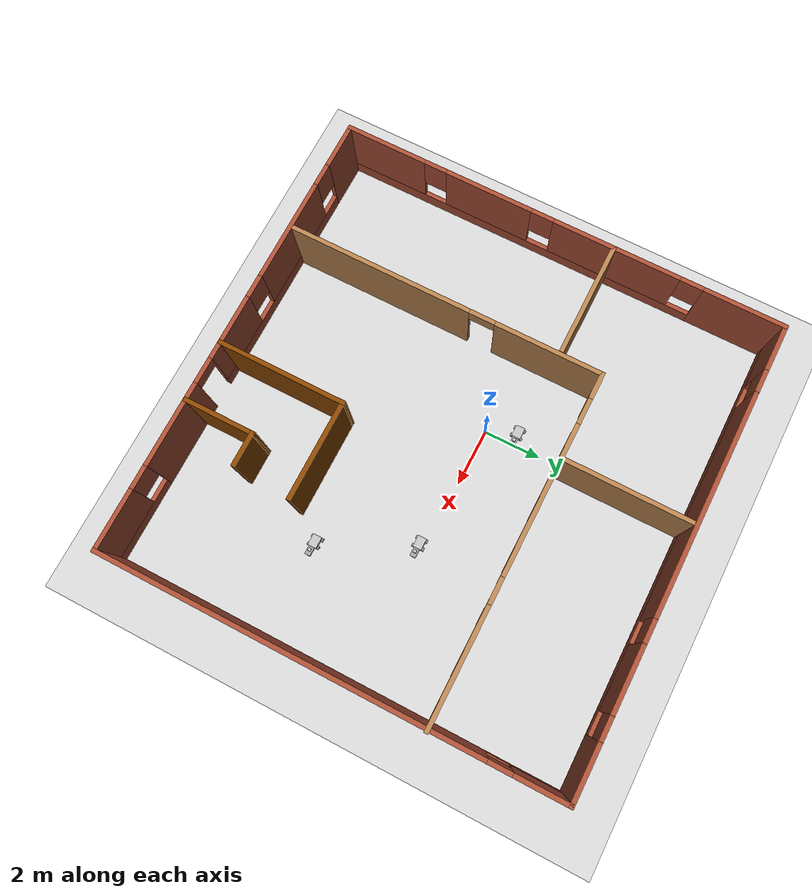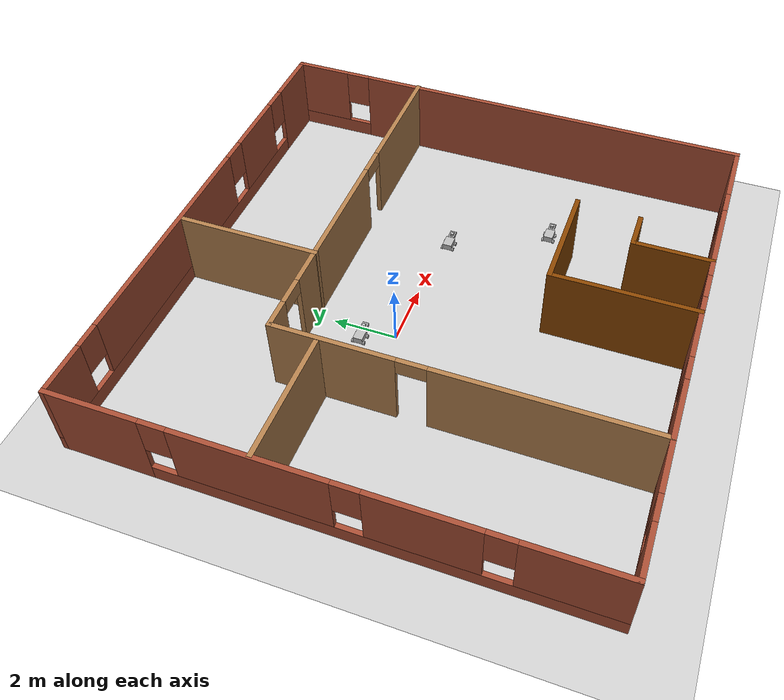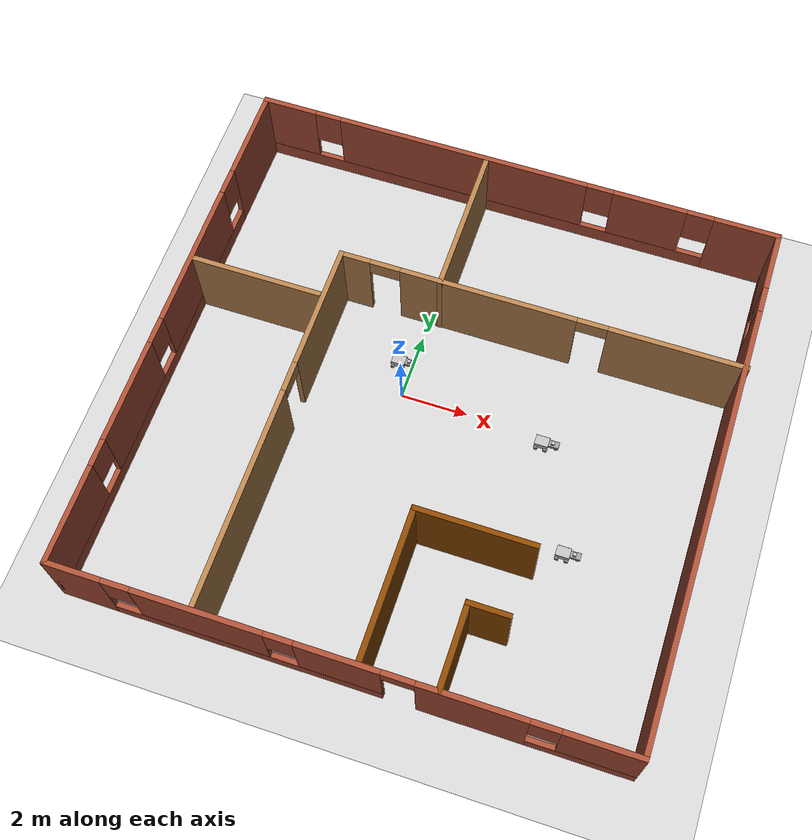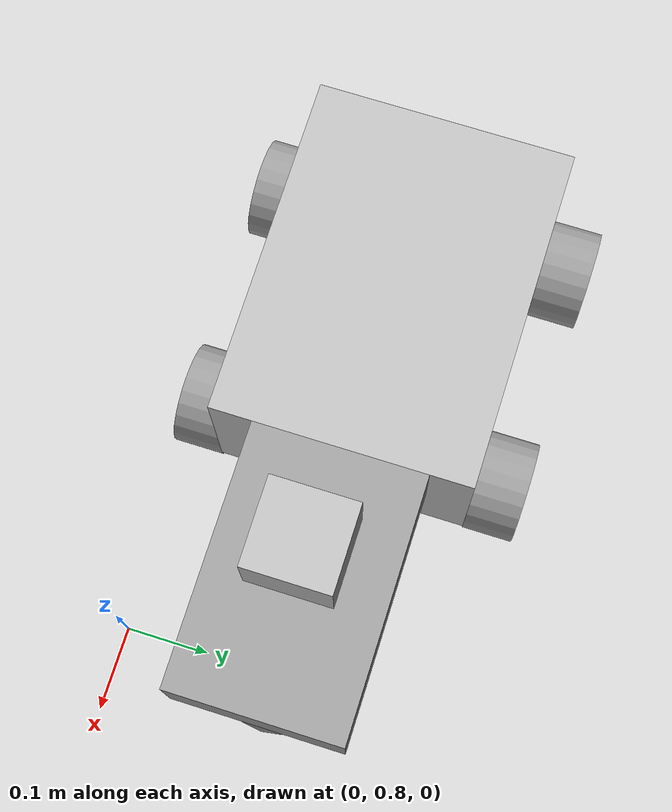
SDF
<sdf version="1.6">
 <world name="default">
  <plugin name="hello" filename="libhello.so"/>
  <light name="sun" type="directional">
   <pose>0 0 10 0 -0 0</pose>
   <diffuse>0.8 0.8 0.8 1</diffuse>
   <specular>0.2 0.2 0.2 1</specular>
   <attenuation>
    <range>1000</range>
    <constant>0.9</constant>
    <linear>0.01</linear>
    <quadratic>0.001</quadratic>
   </attenuation>
   <direction>-0.5 0.1 -0.9</direction>
  </light>
  <model name="ground_plane">
   <static>1</static>
   <link name="link">
    <collision name="collision">
     <geometry><plane><normal>0 0 1</normal><size>100 100</size></plane></geometry>
     <surface><friction><ode><mu>100</mu><mu2>50</mu2></ode></friction></surface>
    </collision>
    <visual name="visual">
     <cast_shadows>0</cast_shadows>
     <geometry><plane><normal>0 0 1</normal><size>100 100</size></plane></geometry>
     <material>
      <script><uri>file://media/materials/scripts/gazebo.material</uri><name>Gazebo/Grey</name></script>
     </material>
    </visual>
   </link>
  </model>
  <gravity>0 0 -9.8</gravity>
  <magnetic_field>6e-06 2.3e-05 -4.2e-05</magnetic_field>
  <atmosphere type="adiabatic"/>
  <physics name="default_physics" default="0" type="ode">
   <max_step_size>0.001</max_step_size>
   <real_time_factor>1</real_time_factor>
   <real_time_update_rate>1000</real_time_update_rate>
  </physics>
  <scene><ambient>0.4 0.4 0.4 1</ambient><background>0.7 0.7 0.7 1</background><shadows>1</shadows></scene>
  <spherical_coordinates>
   <surface_model>EARTH_WGS84</surface_model>
   <latitude_deg>0</latitude_deg>
   <longitude_deg>0</longitude_deg>
   <elevation>0</elevation>
   <heading_deg>0</heading_deg>
  </spherical_coordinates>
  <model name="buillding">
   <pose>1.22192 -0.688168 0 0 -0 0</pose>
   <link name="Wall_11">
    <pose>2.02278 3.31581 0 0 -0 0</pose>
    <visual name="Wall_11_Visual_0">
     <pose>-5.5191 0 1.25 0 -0 0</pose>
     <geometry><box><size>0.961793 0.15 2.5</size></box></geometry>
     <material>
      <script><uri>file://media/materials/scripts/gazebo.material</uri><name>Gazebo/Wood</name></script>
      <ambient>1 1 1 1</ambient>
     </material>
     <meta><layer>0</layer></meta>
    </visual>
    <collision name="Wall_11_Collision_0">
     <geometry><box><size>0.961793 0.15 2.5</size></box></geometry>
     <pose>-5.5191 0 1.25 0 -0 0</pose>
    </collision>
    <visual name="Wall_11_Visual_1">
     <pose>-1.52765 0 1.25 0 -0 0</pose>
     <geometry><box><size>5.2211 0.15 2.5</size></box></geometry>
     <material>
      <script><uri>file://media/materials/scripts/gazebo.material</uri><name>Gazebo/Wood</name></script>
      <ambient>1 1 1 1</ambient>
     </material>
     <meta><layer>0</layer></meta>
    </visual>
    <collision name="Wall_11_Collision_1">
     <geometry><box><size>5.2211 0.15 2.5</size></box></geometry>
     <pose>-1.52765 0 1.25 0 -0 0</pose>
    </collision>
    <visual name="Wall_11_Visual_2">
     <pose>3.99145 0 1.25 0 -0 0</pose>
     <geometry><box><size>4.0171 0.15 2.5</size></box></geometry>
     <material>
      <script><uri>file://media/materials/scripts/gazebo.material</uri><name>Gazebo/Wood</name></script>
      <ambient>1 1 1 1</ambient>
     </material>
     <meta><layer>0</layer></meta>
    </visual>
    <collision name="Wall_11_Collision_2">
     <geometry><box><size>4.0171 0.15 2.5</size></box></geometry>
     <pose>3.99145 0 1.25 0 -0 0</pose>
    </collision>
    <visual name="Wall_11_Visual_3">
     <pose>-4.58821 0 2.25 0 -0 0</pose>
     <geometry><box><size>0.9 0.15 0.5</size></box></geometry>
     <material>
      <script><uri>file://media/materials/scripts/gazebo.material</uri><name>Gazebo/Wood</name></script>
      <ambient>1 1 1 1</ambient>
     </material>
     <meta><layer>0</layer></meta>
    </visual>
    <collision name="Wall_11_Collision_3">
     <geometry><box><size>0.9 0.15 0.5</size></box></geometry>
     <pose>-4.58821 0 2.25 0 -0 0</pose>
    </collision>
    <visual name="Wall_11_Visual_4">
     <pose>1.5329 0 2.25 0 -0 0</pose>
     <geometry><box><size>0.9 0.15 0.5</size></box></geometry>
     <material>
      <script><uri>file://media/materials/scripts/gazebo.material</uri><name>Gazebo/Wood</name></script>
      <ambient>1 1 1 1</ambient>
     </material>
     <meta><layer>0</layer></meta>
    </visual>
    <collision name="Wall_11_Collision_4">
     <geometry><box><size>0.9 0.15 0.5</size></box></geometry>
     <pose>1.5329 0 2.25 0 -0 0</pose>
    </collision>
   </link>
   <link name="Wall_13">
    <collision name="Wall_13_Collision">
     <geometry><box><size>4.5 0.15 2.5</size></box></geometry>
     <pose>0 0 1.25 0 -0 0</pose>
    </collision>
    <visual name="Wall_13_Visual">
     <pose>0 0 1.25 0 -0 0</pose>
     <geometry><box><size>4.5 0.15 2.5</size></box></geometry>
     <material>
      <script><uri>file://media/materials/scripts/gazebo.material</uri><name>Gazebo/Wood</name></script>
      <ambient>1 1 1 1</ambient>
     </material>
     <meta><layer>0</layer></meta>
    </visual>
    <pose>-0.912026 5.47212 0 0 -0 1.5708</pose>
   </link>
   <link name="Wall_15">
    <collision name="Wall_15_Collision">
     <geometry><box><size>4 0.15 2.5</size></box></geometry>
     <pose>0 0 1.25 0 -0 0</pose>
    </collision>
    <visual name="Wall_15_Visual">
     <pose>0 0 1.25 0 -0 0</pose>
     <geometry><box><size>4 0.15 2.5</size></box></geometry>
     <material>
      <script><uri>file://media/materials/scripts/gazebo.material</uri><name>Gazebo/Wood</name></script>
      <ambient>1 1 1 1</ambient>
     </material>
     <meta><layer>0</layer></meta>
    </visual>
    <pose>-5.9876 1.85479 0 0 -0 0</pose>
   </link>
   <link name="Wall_17">
    <collision name="Wall_17_Collision">
     <geometry><box><size>4.5 0.15 2.5</size></box></geometry>
     <pose>0 0 1.25 0 -0 0</pose>
    </collision>
    <visual name="Wall_17_Visual">
     <pose>0 0 1.25 0 -0 0</pose>
     <geometry><box><size>4.5 0.15 2.5</size></box></geometry>
     <material>
      <script><uri>file://media/materials/scripts/gazebo.material</uri><name>Gazebo/Grey</name></script>
      <ambient>0.533333 0.266667 0 1</ambient>
     </material>
     <meta><layer>0</layer></meta>
    </visual>
    <pose>0.565482 -5.60919 0 0 -0 1.5708</pose>
   </link>
   <link name="Wall_19">
    <collision name="Wall_19_Collision">
     <geometry><box><size>3.5 0.15 2.5</size></box></geometry>
     <pose>0 0 1.25 0 -0 0</pose>
    </collision>
    <visual name="Wall_19_Visual">
     <pose>0 0 1.25 0 -0 0</pose>
     <geometry><box><size>3.5 0.15 2.5</size></box></geometry>
     <material>
      <script><uri>file://media/materials/scripts/gazebo.material</uri><name>Gazebo/Grey</name></script>
      <ambient>0.533333 0.266667 0 1</ambient>
     </material>
     <meta><layer>0</layer></meta>
    </visual>
    <pose>2.24048 -3.43419 0 0 -0 0</pose>
   </link>
   <link name="Wall_21">
    <collision name="Wall_21_Collision">
     <geometry><box><size>2.5 0.15 2.5</size></box></geometry>
     <pose>0 0 1.25 0 -0 0</pose>
    </collision>
    <visual name="Wall_21_Visual">
     <pose>0 0 1.25 0 -0 0</pose>
     <geometry><box><size>2.5 0.15 2.5</size></box></geometry>
     <material>
      <script><uri>file://media/materials/scripts/gazebo.material</uri><name>Gazebo/Grey</name></script>
      <ambient>0.533333 0.266667 0 1</ambient>
     </material>
     <meta><layer>0</layer></meta>
    </visual>
    <pose>2.67621 -6.60919 0 0 -0 1.5708</pose>
   </link>
   <link name="Wall_22">
    <collision name="Wall_22_Collision">
     <geometry><box><size>1.25 0.15 2.5</size></box></geometry>
     <pose>0 0 1.25 0 -0 0</pose>
    </collision>
    <visual name="Wall_22_Visual">
     <pose>0 0 1.25 0 -0 0</pose>
     <geometry><box><size>1.25 0.15 2.5</size></box></geometry>
     <material>
      <script><uri>file://media/materials/scripts/gazebo.material</uri><name>Gazebo/Grey</name></script>
      <ambient>0.533333 0.266667 0 1</ambient>
     </material>
     <meta><layer>0</layer></meta>
    </visual>
    <pose>3.22621 -5.43419 0 0 -0 0</pose>
   </link>
   <link name="Wall_4">
    <pose>-7.94778 0 0 0 0 -1.5708</pose>
    <visual name="Wall_4_Visual_0">
     <pose>-6.43687 0 1.25 0 -0 0</pose>
     <geometry><box><size>2.87627 0.15 2.5</size></box></geometry>
     <material>
      <script><uri>file://media/materials/scripts/gazebo.material</uri><name>Gazebo/Bricks</name></script>
      <ambient>1 1 1 1</ambient>
     </material>
     <meta><layer>0</layer></meta>
    </visual>
    <collision name="Wall_4_Collision_0">
     <geometry><box><size>2.87627 0.15 2.5</size></box></geometry>
     <pose>-6.43687 0 1.25 0 -0 0</pose>
    </collision>
    <visual name="Wall_4_Visual_1">
     <pose>1.43813 0 0.25 0 -0 0</pose>
     <geometry><box><size>12.8737 0.15 0.5</size></box></geometry>
     <material>
      <script><uri>file://media/materials/scripts/gazebo.material</uri><name>Gazebo/Bricks</name></script>
      <ambient>1 1 1 1</ambient>
     </material>
     <meta><layer>0</layer></meta>
    </visual>
    <collision name="Wall_4_Collision_1">
     <geometry><box><size>12.8737 0.15 0.5</size></box></geometry>
     <pose>1.43813 0 0.25 0 -0 0</pose>
    </collision>
    <visual name="Wall_4_Visual_2">
     <pose>-1.96033 0 1.5 0 -0 0</pose>
     <geometry><box><size>4.47682 0.15 2</size></box></geometry>
     <material>
      <script><uri>file://media/materials/scripts/gazebo.material</uri><name>Gazebo/Bricks</name></script>
      <ambient>1 1 1 1</ambient>
     </material>
     <meta><layer>0</layer></meta>
    </visual>
    <collision name="Wall_4_Collision_2">
     <geometry><box><size>4.47682 0.15 2</size></box></geometry>
     <pose>-1.96033 0 1.5 0 -0 0</pose>
    </collision>
    <visual name="Wall_4_Visual_3">
     <pose>2.6305 0 1.5 0 -0 0</pose>
     <geometry><box><size>3.10484 0.15 2</size></box></geometry>
     <material>
      <script><uri>file://media/materials/scripts/gazebo.material</uri><name>Gazebo/Bricks</name></script>
      <ambient>1 1 1 1</ambient>
     </material>
     <meta><layer>0</layer></meta>
    </visual>
    <collision name="Wall_4_Collision_3">
     <geometry><box><size>3.10484 0.15 2</size></box></geometry>
     <pose>2.6305 0 1.5 0 -0 0</pose>
    </collision>
    <visual name="Wall_4_Visual_4">
     <pose>6.42896 0 1.5 0 -0 0</pose>
     <geometry><box><size>2.89208 0.15 2</size></box></geometry>
     <material>
      <script><uri>file://media/materials/scripts/gazebo.material</uri><name>Gazebo/Bricks</name></script>
      <ambient>1 1 1 1</ambient>
     </material>
     <meta><layer>0</layer></meta>
    </visual>
    <collision name="Wall_4_Collision_4">
     <geometry><box><size>2.89208 0.15 2</size></box></geometry>
     <pose>6.42896 0 1.5 0 -0 0</pose>
    </collision>
    <visual name="Wall_4_Visual_5">
     <pose>-4.59873 0 1.9 0 -0 0</pose>
     <geometry><box><size>0.8 0.15 1.2</size></box></geometry>
     <material>
      <script><uri>file://media/materials/scripts/gazebo.material</uri><name>Gazebo/Bricks</name></script>
      <ambient>1 1 1 1</ambient>
     </material>
     <meta><layer>0</layer></meta>
    </visual>
    <collision name="Wall_4_Collision_5">
     <geometry><box><size>0.8 0.15 1.2</size></box></geometry>
     <pose>-4.59873 0 1.9 0 -0 0</pose>
    </collision>
    <visual name="Wall_4_Visual_6">
     <pose>0.678082 0 1.9 0 -0 0</pose>
     <geometry><box><size>0.8 0.15 1.2</size></box></geometry>
     <material>
      <script><uri>file://media/materials/scripts/gazebo.material</uri><name>Gazebo/Bricks</name></script>
      <ambient>1 1 1 1</ambient>
     </material>
     <meta><layer>0</layer></meta>
    </visual>
    <collision name="Wall_4_Collision_6">
     <geometry><box><size>0.8 0.15 1.2</size></box></geometry>
     <pose>0.678082 0 1.9 0 -0 0</pose>
    </collision>
    <visual name="Wall_4_Visual_7">
     <pose>4.58293 0 1.9 0 -0 0</pose>
     <geometry><box><size>0.8 0.15 1.2</size></box></geometry>
     <material>
      <script><uri>file://media/materials/scripts/gazebo.material</uri><name>Gazebo/Bricks</name></script>
      <ambient>1 1 1 1</ambient>
     </material>
     <meta><layer>0</layer></meta>
    </visual>
    <collision name="Wall_4_Collision_7">
     <geometry><box><size>0.8 0.15 1.2</size></box></geometry>
     <pose>4.58293 0 1.9 0 -0 0</pose>
    </collision>
   </link>
   <link name="Wall_5">
    <pose>-0.022778 -7.8 0 0 -0 0</pose>
    <visual name="Wall_5_Visual_0">
     <pose>-7.1775 0 1.25 0 -0 0</pose>
     <geometry><box><size>1.64501 0.15 2.5</size></box></geometry>
     <material>
      <script><uri>file://media/materials/scripts/gazebo.material</uri><name>Gazebo/Bricks</name></script>
      <ambient>1 1 1 1</ambient>
     </material>
     <meta><layer>0</layer></meta>
    </visual>
    <collision name="Wall_5_Collision_0">
     <geometry><box><size>1.64501 0.15 2.5</size></box></geometry>
     <pose>-7.1775 0 1.25 0 -0 0</pose>
    </collision>
    <visual name="Wall_5_Visual_1">
     <pose>3.56828 0 1.25 0 -0 0</pose>
     <geometry><box><size>2.94931 0.15 2.5</size></box></geometry>
     <material>
      <script><uri>file://media/materials/scripts/gazebo.material</uri><name>Gazebo/Bricks</name></script>
      <ambient>1 1 1 1</ambient>
     </material>
     <meta><layer>0</layer></meta>
    </visual>
    <collision name="Wall_5_Collision_1">
     <geometry><box><size>2.94931 0.15 2.5</size></box></geometry>
     <pose>3.56828 0 1.25 0 -0 0</pose>
    </collision>
    <visual name="Wall_5_Visual_2">
     <pose>-2.58068 0 0.25 0 -0 0</pose>
     <geometry><box><size>7.54861 0.15 0.5</size></box></geometry>
     <material>
      <script><uri>file://media/materials/scripts/gazebo.material</uri><name>Gazebo/Bricks</name></script>
      <ambient>1 1 1 1</ambient>
     </material>
     <meta><layer>0</layer></meta>
    </visual>
    <collision name="Wall_5_Collision_2">
     <geometry><box><size>7.54861 0.15 0.5</size></box></geometry>
     <pose>-2.58068 0 0.25 0 -0 0</pose>
    </collision>
    <visual name="Wall_5_Visual_3">
     <pose>6.52147 0 0.25 0 -0 0</pose>
     <geometry><box><size>2.95707 0.15 0.5</size></box></geometry>
     <material>
      <script><uri>file://media/materials/scripts/gazebo.material</uri><name>Gazebo/Bricks</name></script>
      <ambient>1 1 1 1</ambient>
     </material>
     <meta><layer>0</layer></meta>
    </visual>
    <collision name="Wall_5_Collision_3">
     <geometry><box><size>2.95707 0.15 0.5</size></box></geometry>
     <pose>6.52147 0 0.25 0 -0 0</pose>
    </collision>
    <visual name="Wall_5_Visual_4">
     <pose>-3.73873 0 1.5 0 -0 0</pose>
     <geometry><box><size>3.63252 0.15 2</size></box></geometry>
     <material>
      <script><uri>file://media/materials/scripts/gazebo.material</uri><name>Gazebo/Bricks</name></script>
      <ambient>1 1 1 1</ambient>
     </material>
     <meta><layer>0</layer></meta>
    </visual>
    <collision name="Wall_5_Collision_4">
     <geometry><box><size>3.63252 0.15 2</size></box></geometry>
     <pose>-3.73873 0 1.5 0 -0 0</pose>
    </collision>
    <visual name="Wall_5_Visual_5">
     <pose>0.035579 0 1.5 0 -0 0</pose>
     <geometry><box><size>2.31609 0.15 2</size></box></geometry>
     <material>
      <script><uri>file://media/materials/scripts/gazebo.material</uri><name>Gazebo/Bricks</name></script>
      <ambient>1 1 1 1</ambient>
     </material>
     <meta><layer>0</layer></meta>
    </visual>
    <collision name="Wall_5_Collision_5">
     <geometry><box><size>2.31609 0.15 2</size></box></geometry>
     <pose>0.035579 0 1.5 0 -0 0</pose>
    </collision>
    <visual name="Wall_5_Visual_6">
     <pose>0.035579 0 1.5 0 -0 0</pose>
     <geometry><box><size>2.31609 0.15 2</size></box></geometry>
     <material>
      <script><uri>file://media/materials/scripts/gazebo.material</uri><name>Gazebo/Bricks</name></script>
      <ambient>1 1 1 1</ambient>
     </material>
     <meta><layer>0</layer></meta>
    </visual>
    <collision name="Wall_5_Collision_6">
     <geometry><box><size>2.31609 0.15 2</size></box></geometry>
     <pose>0.035579 0 1.5 0 -0 0</pose>
    </collision>
    <visual name="Wall_5_Visual_7">
     <pose>6.92147 0 1.5 0 -0 0</pose>
     <geometry><box><size>2.15707 0.15 2</size></box></geometry>
     <material>
      <script><uri>file://media/materials/scripts/gazebo.material</uri><name>Gazebo/Bricks</name></script>
      <ambient>1 1 1 1</ambient>
     </material>
     <meta><layer>0</layer></meta>
    </visual>
    <collision name="Wall_5_Collision_7">
     <geometry><box><size>2.15707 0.15 2</size></box></geometry>
     <pose>6.92147 0 1.5 0 -0 0</pose>
    </collision>
    <visual name="Wall_5_Visual_8">
     <pose>-5.95499 0 1.9 0 -0 0</pose>
     <geometry><box><size>0.8 0.15 1.2</size></box></geometry>
     <material>
      <script><uri>file://media/materials/scripts/gazebo.material</uri><name>Gazebo/Bricks</name></script>
      <ambient>1 1 1 1</ambient>
     </material>
     <meta><layer>0</layer></meta>
    </visual>
    <collision name="Wall_5_Collision_8">
     <geometry><box><size>0.8 0.15 1.2</size></box></geometry>
     <pose>-5.95499 0 1.9 0 -0 0</pose>
    </collision>
    <visual name="Wall_5_Visual_9">
     <pose>5.44293 0 1.9 0 -0 0</pose>
     <geometry><box><size>0.8 0.15 1.2</size></box></geometry>
     <material>
      <script><uri>file://media/materials/scripts/gazebo.material</uri><name>Gazebo/Bricks</name></script>
      <ambient>1 1 1 1</ambient>
     </material>
     <meta><layer>0</layer></meta>
    </visual>
    <collision name="Wall_5_Collision_9">
     <geometry><box><size>0.8 0.15 1.2</size></box></geometry>
     <pose>5.44293 0 1.9 0 -0 0</pose>
    </collision>
    <visual name="Wall_5_Visual_10">
     <pose>-1.52246 0 1.9 0 -0 0</pose>
     <geometry><box><size>0.8 0.15 1.2</size></box></geometry>
     <material>
      <script><uri>file://media/materials/scripts/gazebo.material</uri><name>Gazebo/Bricks</name></script>
      <ambient>1 1 1 1</ambient>
     </material>
     <meta><layer>0</layer></meta>
    </visual>
    <collision name="Wall_5_Collision_10">
     <geometry><box><size>0.8 0.15 1.2</size></box></geometry>
     <pose>-1.52246 0 1.9 0 -0 0</pose>
    </collision>
    <visual name="Wall_5_Visual_11">
     <pose>1.64362 0 2.25 0 -0 0</pose>
     <geometry><box><size>0.9 0.15 0.5</size></box></geometry>
     <material>
      <script><uri>file://media/materials/scripts/gazebo.material</uri><name>Gazebo/Bricks</name></script>
      <ambient>1 1 1 1</ambient>
     </material>
     <meta><layer>0</layer></meta>
    </visual>
    <collision name="Wall_5_Collision_11">
     <geometry><box><size>0.9 0.15 0.5</size></box></geometry>
     <pose>1.64362 0 2.25 0 -0 0</pose>
    </collision>
    <visual name="Wall_5_Visual_12">
     <pose>1.64362 0 2.25 0 -0 0</pose>
     <geometry><box><size>0.9 0.15 0.5</size></box></geometry>
     <material>
      <script><uri>file://media/materials/scripts/gazebo.material</uri><name>Gazebo/Bricks</name></script>
      <ambient>1 1 1 1</ambient>
     </material>
     <meta><layer>0</layer></meta>
    </visual>
    <collision name="Wall_5_Collision_12">
     <geometry><box><size>0.9 0.15 0.5</size></box></geometry>
     <pose>1.64362 0 2.25 0 -0 0</pose>
    </collision>
   </link>
   <link name="Wall_6">
    <pose>7.90222 0 0 0 -0 1.5708</pose>
    <visual name="Wall_6_Visual_0">
     <pose>-1.34563 0 1.25 0 -0 0</pose>
     <geometry><box><size>13.0587 0.15 2.5</size></box></geometry>
     <material>
      <script><uri>file://media/materials/scripts/gazebo.material</uri><name>Gazebo/Bricks</name></script>
      <ambient>1 1 1 1</ambient>
     </material>
     <meta><layer>0</layer></meta>
    </visual>
    <collision name="Wall_6_Collision_0">
     <geometry><box><size>13.0587 0.15 2.5</size></box></geometry>
     <pose>-1.34563 0 1.25 0 -0 0</pose>
    </collision>
    <visual name="Wall_6_Visual_1">
     <pose>6.52937 0 0.25 0 -0 0</pose>
     <geometry><box><size>2.69126 0.15 0.5</size></box></geometry>
     <material>
      <script><uri>file://media/materials/scripts/gazebo.material</uri><name>Gazebo/Bricks</name></script>
      <ambient>1 1 1 1</ambient>
     </material>
     <meta><layer>0</layer></meta>
    </visual>
    <collision name="Wall_6_Collision_1">
     <geometry><box><size>2.69126 0.15 0.5</size></box></geometry>
     <pose>6.52937 0 0.25 0 -0 0</pose>
    </collision>
    <visual name="Wall_6_Visual_2">
     <pose>6.92937 0 1.5 0 -0 0</pose>
     <geometry><box><size>1.89126 0.15 2</size></box></geometry>
     <material>
      <script><uri>file://media/materials/scripts/gazebo.material</uri><name>Gazebo/Bricks</name></script>
      <ambient>1 1 1 1</ambient>
     </material>
     <meta><layer>0</layer></meta>
    </visual>
    <collision name="Wall_6_Collision_2">
     <geometry><box><size>1.89126 0.15 2</size></box></geometry>
     <pose>6.92937 0 1.5 0 -0 0</pose>
    </collision>
    <visual name="Wall_6_Visual_3">
     <pose>5.58374 0 1.9 0 -0 0</pose>
     <geometry><box><size>0.8 0.15 1.2</size></box></geometry>
     <material>
      <script><uri>file://media/materials/scripts/gazebo.material</uri><name>Gazebo/Bricks</name></script>
      <ambient>1 1 1 1</ambient>
     </material>
     <meta><layer>0</layer></meta>
    </visual>
    <collision name="Wall_6_Collision_3">
     <geometry><box><size>0.8 0.15 1.2</size></box></geometry>
     <pose>5.58374 0 1.9 0 -0 0</pose>
    </collision>
   </link>
   <link name="Wall_7">
    <pose>-0.022778 7.8 0 0 -0 3.14159</pose>
    <visual name="Wall_7_Visual_0">
     <pose>-7.00941 0 1.25 0 -0 0</pose>
     <geometry><box><size>1.98118 0.15 2.5</size></box></geometry>
     <material>
      <script><uri>file://media/materials/scripts/gazebo.material</uri><name>Gazebo/Bricks</name></script>
      <ambient>1 1 1 1</ambient>
     </material>
     <meta><layer>0</layer></meta>
    </visual>
    <collision name="Wall_7_Collision_0">
     <geometry><box><size>1.98118 0.15 2.5</size></box></geometry>
     <pose>-7.00941 0 1.25 0 -0 0</pose>
    </collision>
    <visual name="Wall_7_Visual_1">
     <pose>0.990588 0 0.25 0 -0 0</pose>
     <geometry><box><size>14.0188 0.15 0.5</size></box></geometry>
     <material>
      <script><uri>file://media/materials/scripts/gazebo.material</uri><name>Gazebo/Bricks</name></script>
      <ambient>1 1 1 1</ambient>
     </material>
     <meta><layer>0</layer></meta>
    </visual>
    <collision name="Wall_7_Collision_1">
     <geometry><box><size>14.0188 0.15 0.5</size></box></geometry>
     <pose>0.990588 0 0.25 0 -0 0</pose>
    </collision>
    <visual name="Wall_7_Visual_2">
     <pose>-4.10614 0 1.5 0 -0 0</pose>
     <geometry><box><size>2.22537 0.15 2</size></box></geometry>
     <material>
      <script><uri>file://media/materials/scripts/gazebo.material</uri><name>Gazebo/Bricks</name></script>
      <ambient>1 1 1 1</ambient>
     </material>
     <meta><layer>0</layer></meta>
    </visual>
    <collision name="Wall_7_Collision_2">
     <geometry><box><size>2.22537 0.15 2</size></box></geometry>
     <pose>-4.10614 0 1.5 0 -0 0</pose>
    </collision>
    <visual name="Wall_7_Visual_3">
     <pose>1.66318 0 1.5 0 -0 0</pose>
     <geometry><box><size>7.71326 0.15 2</size></box></geometry>
     <material>
      <script><uri>file://media/materials/scripts/gazebo.material</uri><name>Gazebo/Bricks</name></script>
      <ambient>1 1 1 1</ambient>
     </material>
     <meta><layer>0</layer></meta>
    </visual>
    <collision name="Wall_7_Collision_3">
     <geometry><box><size>7.71326 0.15 2</size></box></geometry>
     <pose>1.66318 0 1.5 0 -0 0</pose>
    </collision>
    <visual name="Wall_7_Visual_4">
     <pose>7.15991 0 1.5 0 -0 0</pose>
     <geometry><box><size>1.68019 0.15 2</size></box></geometry>
     <material>
      <script><uri>file://media/materials/scripts/gazebo.material</uri><name>Gazebo/Bricks</name></script>
      <ambient>1 1 1 1</ambient>
     </material>
     <meta><layer>0</layer></meta>
    </visual>
    <collision name="Wall_7_Collision_4">
     <geometry><box><size>1.68019 0.15 2</size></box></geometry>
     <pose>7.15991 0 1.5 0 -0 0</pose>
    </collision>
    <visual name="Wall_7_Visual_5">
     <pose>-5.61882 0 1.9 0 -0 0</pose>
     <geometry><box><size>0.8 0.15 1.2</size></box></geometry>
     <material>
      <script><uri>file://media/materials/scripts/gazebo.material</uri><name>Gazebo/Bricks</name></script>
      <ambient>1 1 1 1</ambient>
     </material>
     <meta><layer>0</layer></meta>
    </visual>
    <collision name="Wall_7_Collision_5">
     <geometry><box><size>0.8 0.15 1.2</size></box></geometry>
     <pose>-5.61882 0 1.9 0 -0 0</pose>
    </collision>
    <visual name="Wall_7_Visual_6">
     <pose>-2.59345 0 1.9 0 -0 0</pose>
     <geometry><box><size>0.8 0.15 1.2</size></box></geometry>
     <material>
      <script><uri>file://media/materials/scripts/gazebo.material</uri><name>Gazebo/Bricks</name></script>
      <ambient>1 1 1 1</ambient>
     </material>
     <meta><layer>0</layer></meta>
    </visual>
    <collision name="Wall_7_Collision_6">
     <geometry><box><size>0.8 0.15 1.2</size></box></geometry>
     <pose>-2.59345 0 1.9 0 -0 0</pose>
    </collision>
    <visual name="Wall_7_Visual_7">
     <pose>5.91981 0 1.9 0 -0 0</pose>
     <geometry><box><size>0.8 0.15 1.2</size></box></geometry>
     <material>
      <script><uri>file://media/materials/scripts/gazebo.material</uri><name>Gazebo/Bricks</name></script>
      <ambient>1 1 1 1</ambient>
     </material>
     <meta><layer>0</layer></meta>
    </visual>
    <collision name="Wall_7_Collision_7">
     <geometry><box><size>0.8 0.15 1.2</size></box></geometry>
     <pose>5.91981 0 1.9 0 -0 0</pose>
    </collision>
   </link>
   <link name="Wall_9">
    <pose>-3.90222 -2.23419 0 0 -0 1.5708</pose>
    <visual name="Wall_9_Visual_0">
     <pose>-2.34739 0 1.25 0 -0 0</pose>
     <geometry><box><size>6.55522 0.15 2.5</size></box></geometry>
     <material>
      <script><uri>file://media/materials/scripts/gazebo.material</uri><name>Gazebo/Wood</name></script>
      <ambient>1 1 1 1</ambient>
     </material>
     <meta><layer>0</layer></meta>
    </visual>
    <collision name="Wall_9_Collision_0">
     <geometry><box><size>6.55522 0.15 2.5</size></box></geometry>
     <pose>-2.34739 0 1.25 0 -0 0</pose>
    </collision>
    <visual name="Wall_9_Visual_1">
     <pose>3.72761 0 1.25 0 -0 0</pose>
     <geometry><box><size>3.79478 0.15 2.5</size></box></geometry>
     <material>
      <script><uri>file://media/materials/scripts/gazebo.material</uri><name>Gazebo/Wood</name></script>
      <ambient>1 1 1 1</ambient>
     </material>
     <meta><layer>0</layer></meta>
    </visual>
    <collision name="Wall_9_Collision_1">
     <geometry><box><size>3.79478 0.15 2.5</size></box></geometry>
     <pose>3.72761 0 1.25 0 -0 0</pose>
    </collision>
    <visual name="Wall_9_Visual_2">
     <pose>1.38022 0 2.25 0 -0 0</pose>
     <geometry><box><size>0.9 0.15 0.5</size></box></geometry>
     <material>
      <script><uri>file://media/materials/scripts/gazebo.material</uri><name>Gazebo/Wood</name></script>
      <ambient>1 1 1 1</ambient>
     </material>
     <meta><layer>0</layer></meta>
    </visual>
    <collision name="Wall_9_Collision_2">
     <geometry><box><size>0.9 0.15 0.5</size></box></geometry>
     <pose>1.38022 0 2.25 0 -0 0</pose>
    </collision>
   </link>
   <static>1</static>
  </model>
  <model name="robot">
   <link name="chassis">
    <pose>0 0 0.16 0 -0 0</pose>
    <inertial>
     <mass>1</mass>
     <inertia><ixx>1</ixx><ixy>0</ixy><ixz>0</ixz><iyy>1</iyy><iyz>0</iyz><izz>1</izz></inertia>
    </inertial>
    <visual name="visual">
     <geometry><box><size>0.4 0.3 0.2</size></box></geometry>
     <material>
      <shader type="pixel"><normal_map>__default__</normal_map></shader>
      <emissive>0 0 0 1</emissive>
     </material>
    </visual>
    <collision name="collision">
     <geometry><box><size>0.4 0.3 0.2</size></box></geometry>
     <surface>
      <friction>
       <ode><mu>1</mu><mu2>1</mu2><fdir1>0 0 0</fdir1><slip1>0</slip1><slip2>0</slip2></ode>
       <torsional>
        <coefficient>1</coefficient>
        <patch_radius>0</patch_radius>
        <surface_radius>0</surface_radius>
        <use_patch_radius>1</use_patch_radius>
        <ode><slip>0</slip></ode>
       </torsional>
      </friction>
      <bounce><restitution_coefficient>0</restitution_coefficient><threshold>1e+06</threshold></bounce>
      <contact>
       <collide_without_contact>0</collide_without_contact>
       <collide_without_contact_bitmask>1</collide_without_contact_bitmask>
       <collide_bitmask>1</collide_bitmask>
       <ode>
        <soft_cfm>0</soft_cfm>
        <soft_erp>0.2</soft_erp>
        <kp>1e+13</kp>
        <kd>1</kd>
        <max_vel>0.01</max_vel>
        <min_depth>0</min_depth>
       </ode>
       <bullet>
        <split_impulse>1</split_impulse>
        <split_impulse_penetration_threshold>-0.01</split_impulse_penetration_threshold>
        <soft_cfm>0</soft_cfm>
        <soft_erp>0.2</soft_erp>
        <kp>1e+13</kp>
        <kd>1</kd>
       </bullet>
      </contact>
     </surface>
    </collision>
   </link>
   <link name="link_0_clone">
    <pose>-0.14 -0.180006 0.06 1.5707 -0 0</pose>
    <inertial>
     <mass>1</mass>
     <inertia><ixx>0.145833</ixx><ixy>0</ixy><ixz>0</ixz><iyy>0.145833</iyy><iyz>0</iyz><izz>0.125</izz></inertia>
    </inertial>
    <visual name="visual">
     <geometry><cylinder><radius>0.06</radius><length>0.06</length></cylinder></geometry>
     <material>
      <lighting>1</lighting>
      <script><uri>file://media/materials/scripts/gazebo.material</uri><name>Gazebo/Grey</name></script>
      <shader type="pixel"><normal_map>__default__</normal_map></shader>
      <ambient>0.3 0.3 0.3 1</ambient>
      <diffuse>0.7 0.7 0.7 1</diffuse>
      <specular>0.01 0.01 0.01 1</specular>
      <emissive>0 0 0 1</emissive>
     </material>
    </visual>
    <collision name="collision">
     <geometry><cylinder><radius>0.06</radius><length>0.06</length></cylinder></geometry>
     <surface>
      <friction>
       <ode><mu>1</mu><mu2>1</mu2><fdir1>0 0 0</fdir1><slip1>0</slip1><slip2>0</slip2></ode>
       <torsional>
        <coefficient>1</coefficient>
        <patch_radius>0</patch_radius>
        <surface_radius>0</surface_radius>
        <use_patch_radius>1</use_patch_radius>
        <ode><slip>0</slip></ode>
       </torsional>
      </friction>
      <bounce><restitution_coefficient>0</restitution_coefficient><threshold>1e+06</threshold></bounce>
      <contact>
       <collide_without_contact>0</collide_without_contact>
       <collide_without_contact_bitmask>1</collide_without_contact_bitmask>
       <collide_bitmask>1</collide_bitmask>
       <ode>
        <soft_cfm>0</soft_cfm>
        <soft_erp>0.2</soft_erp>
        <kp>1e+13</kp>
        <kd>1</kd>
        <max_vel>0.01</max_vel>
        <min_depth>0</min_depth>
       </ode>
       <bullet>
        <split_impulse>1</split_impulse>
        <split_impulse_penetration_threshold>-0.01</split_impulse_penetration_threshold>
        <soft_cfm>0</soft_cfm>
        <soft_erp>0.2</soft_erp>
        <kp>1e+13</kp>
        <kd>1</kd>
       </bullet>
      </contact>
     </surface>
    </collision>
   </link>
   <link name="link_0_clone_0">
    <pose>0.14 -0.180006 0.06 1.5707 -0 0</pose>
    <inertial>
     <mass>1</mass>
     <inertia><ixx>0.145833</ixx><ixy>0</ixy><ixz>0</ixz><iyy>0.145833</iyy><iyz>0</iyz><izz>0.125</izz></inertia>
    </inertial>
    <visual name="visual">
     <geometry><cylinder><radius>0.06</radius><length>0.06</length></cylinder></geometry>
     <material>
      <lighting>1</lighting>
      <script><uri>file://media/materials/scripts/gazebo.material</uri><name>Gazebo/Grey</name></script>
      <shader type="pixel"><normal_map>__default__</normal_map></shader>
      <ambient>0.3 0.3 0.3 1</ambient>
      <diffuse>0.7 0.7 0.7 1</diffuse>
      <specular>0.01 0.01 0.01 1</specular>
      <emissive>0 0 0 1</emissive>
     </material>
    </visual>
    <collision name="collision">
     <geometry><cylinder><radius>0.06</radius><length>0.06</length></cylinder></geometry>
     <surface>
      <friction>
       <ode><mu>1</mu><mu2>1</mu2><fdir1>0 0 0</fdir1><slip1>0</slip1><slip2>0</slip2></ode>
       <torsional>
        <coefficient>1</coefficient>
        <patch_radius>0</patch_radius>
        <surface_radius>0</surface_radius>
        <use_patch_radius>1</use_patch_radius>
        <ode><slip>0</slip></ode>
       </torsional>
      </friction>
      <bounce><restitution_coefficient>0</restitution_coefficient><threshold>1e+06</threshold></bounce>
      <contact>
       <collide_without_contact>0</collide_without_contact>
       <collide_without_contact_bitmask>1</collide_without_contact_bitmask>
       <collide_bitmask>1</collide_bitmask>
       <ode>
        <soft_cfm>0</soft_cfm>
        <soft_erp>0.2</soft_erp>
        <kp>1e+13</kp>
        <kd>1</kd>
        <max_vel>0.01</max_vel>
        <min_depth>0</min_depth>
       </ode>
       <bullet>
        <split_impulse>1</split_impulse>
        <split_impulse_penetration_threshold>-0.01</split_impulse_penetration_threshold>
        <soft_cfm>0</soft_cfm>
        <soft_erp>0.2</soft_erp>
        <kp>1e+13</kp>
        <kd>1</kd>
       </bullet>
      </contact>
     </surface>
    </collision>
   </link>
   <link name="link_0_clone_1">
    <pose>-0.14 0.180006 0.06 1.5707 -0 0</pose>
    <inertial>
     <mass>1</mass>
     <inertia><ixx>0.145833</ixx><ixy>0</ixy><ixz>0</ixz><iyy>0.145833</iyy><iyz>0</iyz><izz>0.125</izz></inertia>
    </inertial>
    <visual name="visual">
     <geometry><cylinder><radius>0.06</radius><length>0.06</length></cylinder></geometry>
     <material>
      <lighting>1</lighting>
      <script><uri>file://media/materials/scripts/gazebo.material</uri><name>Gazebo/Grey</name></script>
      <shader type="pixel"><normal_map>__default__</normal_map></shader>
      <ambient>0.3 0.3 0.3 1</ambient>
      <diffuse>0.7 0.7 0.7 1</diffuse>
      <specular>0.01 0.01 0.01 1</specular>
      <emissive>0 0 0 1</emissive>
     </material>
    </visual>
    <collision name="collision">
     <geometry><cylinder><radius>0.06</radius><length>0.06</length></cylinder></geometry>
     <surface>
      <friction>
       <ode><mu>1</mu><mu2>1</mu2><fdir1>0 0 0</fdir1><slip1>0</slip1><slip2>0</slip2></ode>
       <torsional>
        <coefficient>1</coefficient>
        <patch_radius>0</patch_radius>
        <surface_radius>0</surface_radius>
        <use_patch_radius>1</use_patch_radius>
        <ode><slip>0</slip></ode>
       </torsional>
      </friction>
      <bounce><restitution_coefficient>0</restitution_coefficient><threshold>1e+06</threshold></bounce>
      <contact>
       <collide_without_contact>0</collide_without_contact>
       <collide_without_contact_bitmask>1</collide_without_contact_bitmask>
       <collide_bitmask>1</collide_bitmask>
       <ode>
        <soft_cfm>0</soft_cfm>
        <soft_erp>0.2</soft_erp>
        <kp>1e+13</kp>
        <kd>1</kd>
        <max_vel>0.01</max_vel>
        <min_depth>0</min_depth>
       </ode>
       <bullet>
        <split_impulse>1</split_impulse>
        <split_impulse_penetration_threshold>-0.01</split_impulse_penetration_threshold>
        <soft_cfm>0</soft_cfm>
        <soft_erp>0.2</soft_erp>
        <kp>1e+13</kp>
        <kd>1</kd>
       </bullet>
      </contact>
     </surface>
    </collision>
   </link>
   <link name="link_0_clone_2">
    <pose>0.14 0.180006 0.06 1.5707 -0 0</pose>
    <inertial>
     <mass>1</mass>
     <inertia><ixx>0.145833</ixx><ixy>0</ixy><ixz>0</ixz><iyy>0.145833</iyy><iyz>0</iyz><izz>0.125</izz></inertia>
    </inertial>
    <visual name="visual">
     <geometry><cylinder><radius>0.06</radius><length>0.06</length></cylinder></geometry>
     <material>
      <lighting>1</lighting>
      <script><uri>file://media/materials/scripts/gazebo.material</uri><name>Gazebo/Grey</name></script>
      <shader type="pixel"><normal_map>__default__</normal_map></shader>
      <ambient>0.3 0.3 0.3 1</ambient>
      <diffuse>0.7 0.7 0.7 1</diffuse>
      <specular>0.01 0.01 0.01 1</specular>
      <emissive>0 0 0 1</emissive>
     </material>
    </visual>
    <collision name="collision">
     <geometry><cylinder><radius>0.06</radius><length>0.06</length></cylinder></geometry>
     <surface>
      <friction>
       <ode><mu>1</mu><mu2>1</mu2><fdir1>0 0 0</fdir1><slip1>0</slip1><slip2>0</slip2></ode>
       <torsional>
        <coefficient>1</coefficient>
        <patch_radius>0</patch_radius>
        <surface_radius>0</surface_radius>
        <use_patch_radius>1</use_patch_radius>
        <ode><slip>0</slip></ode>
       </torsional>
      </friction>
      <bounce><restitution_coefficient>0</restitution_coefficient><threshold>1e+06</threshold></bounce>
      <contact>
       <collide_without_contact>0</collide_without_contact>
       <collide_without_contact_bitmask>1</collide_without_contact_bitmask>
       <collide_bitmask>1</collide_bitmask>
       <ode>
        <soft_cfm>0</soft_cfm>
        <soft_erp>0.2</soft_erp>
        <kp>1e+13</kp>
        <kd>1</kd>
        <max_vel>0.01</max_vel>
        <min_depth>0</min_depth>
       </ode>
       <bullet>
        <split_impulse>1</split_impulse>
        <split_impulse_penetration_threshold>-0.01</split_impulse_penetration_threshold>
        <soft_cfm>0</soft_cfm>
        <soft_erp>0.2</soft_erp>
        <kp>1e+13</kp>
        <kd>1</kd>
       </bullet>
      </contact>
     </surface>
    </collision>
   </link>
   <link name="link_1_clone">
    <pose>0.35 0 0.21 0 -0 0</pose>
    <inertial>
     <mass>1</mass>
     <inertia>
      <ixx>0.166667</ixx>
      <ixy>0</ixy>
      <ixz>0</ixz>
      <iyy>0.166667</iyy>
      <iyz>0</iyz>
      <izz>0.166667</izz>
     </inertia>
    </inertial>
    <visual name="visual">
     <geometry><box><size>0.3 0.2 0.1</size></box></geometry>
     <material>
      <lighting>1</lighting>
      <script><uri>file://media/materials/scripts/gazebo.material</uri><name>Gazebo/Grey</name></script>
      <shader type="pixel"><normal_map>__default__</normal_map></shader>
      <ambient>0.3 0.3 0.3 1</ambient>
      <diffuse>0.7 0.7 0.7 1</diffuse>
      <specular>0.01 0.01 0.01 1</specular>
      <emissive>0 0 0 1</emissive>
     </material>
    </visual>
    <collision name="collision">
     <geometry><box><size>0.3 0.2 0.1</size></box></geometry>
     <surface>
      <friction>
       <ode><mu>1</mu><mu2>1</mu2><fdir1>0 0 0</fdir1><slip1>0</slip1><slip2>0</slip2></ode>
       <torsional>
        <coefficient>1</coefficient>
        <patch_radius>0</patch_radius>
        <surface_radius>0</surface_radius>
        <use_patch_radius>1</use_patch_radius>
        <ode><slip>0</slip></ode>
       </torsional>
      </friction>
      <bounce><restitution_coefficient>0</restitution_coefficient><threshold>1e+06</threshold></bounce>
      <contact>
       <collide_without_contact>0</collide_without_contact>
       <collide_without_contact_bitmask>1</collide_without_contact_bitmask>
       <collide_bitmask>1</collide_bitmask>
       <ode>
        <soft_cfm>0</soft_cfm>
        <soft_erp>0.2</soft_erp>
        <kp>1e+13</kp>
        <kd>1</kd>
        <max_vel>0.01</max_vel>
        <min_depth>0</min_depth>
       </ode>
       <bullet>
        <split_impulse>1</split_impulse>
        <split_impulse_penetration_threshold>-0.01</split_impulse_penetration_threshold>
        <soft_cfm>0</soft_cfm>
        <soft_erp>0.2</soft_erp>
        <kp>1e+13</kp>
        <kd>1</kd>
       </bullet>
      </contact>
     </surface>
    </collision>
   </link>
   <link name="link_2_clone">
    <pose>0.42 0 0.08 0 -0 0</pose>
    <inertial>
     <mass>1</mass>
     <inertia><ixx>0.1</ixx><ixy>0</ixy><ixz>0</ixz><iyy>0.1</iyy><iyz>0</iyz><izz>0.1</izz></inertia>
    </inertial>
    <visual name="visual">
     <geometry><sphere><radius>0.08</radius></sphere></geometry>
     <material>
      <lighting>1</lighting>
      <script><uri>file://media/materials/scripts/gazebo.material</uri><name>Gazebo/Grey</name></script>
      <shader type="pixel"><normal_map>__default__</normal_map></shader>
      <ambient>0.3 0.3 0.3 1</ambient>
      <diffuse>0.7 0.7 0.7 1</diffuse>
      <specular>0.01 0.01 0.01 1</specular>
      <emissive>0 0 0 1</emissive>
     </material>
    </visual>
    <collision name="collision">
     <geometry><sphere><radius>0.08</radius></sphere></geometry>
     <surface>
      <friction>
       <ode><mu>1</mu><mu2>1</mu2><fdir1>0 0 0</fdir1><slip1>0</slip1><slip2>0</slip2></ode>
       <torsional>
        <coefficient>1</coefficient>
        <patch_radius>0</patch_radius>
        <surface_radius>0</surface_radius>
        <use_patch_radius>1</use_patch_radius>
        <ode><slip>0</slip></ode>
       </torsional>
      </friction>
      <bounce><restitution_coefficient>0</restitution_coefficient><threshold>1e+06</threshold></bounce>
      <contact>
       <collide_without_contact>0</collide_without_contact>
       <collide_without_contact_bitmask>1</collide_without_contact_bitmask>
       <collide_bitmask>1</collide_bitmask>
       <ode>
        <soft_cfm>0</soft_cfm>
        <soft_erp>0.2</soft_erp>
        <kp>1e+13</kp>
        <kd>1</kd>
        <max_vel>0.01</max_vel>
        <min_depth>0</min_depth>
       </ode>
       <bullet>
        <split_impulse>1</split_impulse>
        <split_impulse_penetration_threshold>-0.01</split_impulse_penetration_threshold>
        <soft_cfm>0</soft_cfm>
        <soft_erp>0.2</soft_erp>
        <kp>1e+13</kp>
        <kd>1</kd>
       </bullet>
      </contact>
     </surface>
    </collision>
   </link>
   <model name="depth_camera">
    <link name="link">
     <pose>0 0 0.05 0 -0 0</pose>
     <inertial>
      <mass>0.1</mass>
      <inertia>
       <ixx>0.000166667</ixx>
       <iyy>0.000166667</iyy>
       <izz>0.000166667</izz>
       <ixy>0</ixy>
       <ixz>0</ixz>
       <iyz>0</iyz>
      </inertia>
     </inertial>
     <collision name="collision"><geometry><box><size>0.1 0.1 0.1</size></box></geometry></collision>
     <visual name="visual"><geometry><box><size>0.1 0.1 0.1</size></box></geometry></visual>
     <sensor name="camera" type="depth">
      <camera name="__default__">
       <horizontal_fov>1.047</horizontal_fov>
       <image><width>320</width><height>240</height></image>
       <clip><near>0.1</near><far>100</far></clip>
      </camera>
      <always_on>1</always_on>
      <update_rate>30</update_rate>
      <visualize>1</visualize>
     </sensor>
    </link>
    <pose>0.31707 -0.004098 0.243439 0 -0 0</pose>
   </model>
   <joint name="chassis_JOINT_0" type="revolute">
    <parent>chassis</parent>
    <child>link_0_clone_0</child>
    <axis>
     <xyz>0 0 -1</xyz>
     <use_parent_model_frame>0</use_parent_model_frame>
     <limit>
      <lower>-1.79769e+308</lower>
      <upper>1.79769e+308</upper>
      <effort>-1</effort>
      <velocity>-1</velocity>
     </limit>
     <dynamics>
      <spring_reference>0</spring_reference>
      <spring_stiffness>0</spring_stiffness>
      <damping>0</damping>
     </dynamics>
    </axis>
    <physics>
     <ode><limit><cfm>0</cfm><erp>0.2</erp></limit><suspension><cfm>0</cfm><erp>0.2</erp></suspension></ode>
    </physics>
   </joint>
   <joint name="chassis_JOINT_1" type="revolute">
    <parent>chassis</parent>
    <child>link_0_clone</child>
    <axis>
     <xyz>0 0 -1</xyz>
     <use_parent_model_frame>0</use_parent_model_frame>
     <limit>
      <lower>-1.79769e+308</lower>
      <upper>1.79769e+308</upper>
      <effort>-1</effort>
      <velocity>-1</velocity>
     </limit>
     <dynamics>
      <spring_reference>0</spring_reference>
      <spring_stiffness>0</spring_stiffness>
      <damping>0</damping>
     </dynamics>
    </axis>
    <physics>
     <ode><limit><cfm>0</cfm><erp>0.2</erp></limit><suspension><cfm>0</cfm><erp>0.2</erp></suspension></ode>
    </physics>
   </joint>
   <joint name="chassis_JOINT_2" type="revolute">
    <parent>chassis</parent>
    <child>link_0_clone_2</child>
    <axis>
     <xyz>0 0 1</xyz>
     <use_parent_model_frame>0</use_parent_model_frame>
     <limit>
      <lower>-1.79769e+308</lower>
      <upper>1.79769e+308</upper>
      <effort>-1</effort>
      <velocity>-1</velocity>
     </limit>
     <dynamics>
      <spring_reference>0</spring_reference>
      <spring_stiffness>0</spring_stiffness>
      <damping>0</damping>
     </dynamics>
    </axis>
    <physics>
     <ode><limit><cfm>0</cfm><erp>0.2</erp></limit><suspension><cfm>0</cfm><erp>0.2</erp></suspension></ode>
    </physics>
   </joint>
   <joint name="chassis_JOINT_3" type="revolute">
    <parent>chassis</parent>
    <child>link_0_clone_1</child>
    <axis>
     <xyz>0 0 1</xyz>
     <use_parent_model_frame>0</use_parent_model_frame>
     <limit>
      <lower>-1.79769e+308</lower>
      <upper>1.79769e+308</upper>
      <effort>-1</effort>
      <velocity>-1</velocity>
     </limit>
     <dynamics>
      <spring_reference>0</spring_reference>
      <spring_stiffness>0</spring_stiffness>
      <damping>0</damping>
     </dynamics>
    </axis>
    <physics>
     <ode><limit><cfm>0</cfm><erp>0.2</erp></limit><suspension><cfm>0</cfm><erp>0.2</erp></suspension></ode>
    </physics>
   </joint>
   <joint name="chassis_JOINT_4" type="fixed">
    <parent>chassis</parent>
    <child>link_1_clone</child>
    <physics>
     <ode><limit><cfm>0</cfm><erp>0.2</erp></limit><suspension><cfm>0</cfm><erp>0.2</erp></suspension></ode>
    </physics>
   </joint>
   <joint name="link_JOINT_6" type="fixed">
    <parent>depth_camera::link</parent>
    <child>link_1_clone</child>
    <physics>
     <ode><limit><cfm>0</cfm><erp>0.2</erp></limit><suspension><cfm>0</cfm><erp>0.2</erp></suspension></ode>
    </physics>
   </joint>
   <joint name="link_1_clone_JOINT_5" type="ball">
    <parent>link_1_clone</parent>
    <child>link_2_clone</child>
    <physics>
     <ode><limit><cfm>0</cfm><erp>0.2</erp></limit><suspension><cfm>0</cfm><erp>0.2</erp></suspension></ode>
    </physics>
   </joint>
   <static>1</static>
   <pose>-0.427572 0.997056 0 0 -0 0</pose>
  </model>
  <model name="robot_0">
   <link name="chassis">
    <pose>0 0 0.16 0 -0 0</pose>
    <inertial>
     <mass>1</mass>
     <inertia><ixx>1</ixx><ixy>0</ixy><ixz>0</ixz><iyy>1</iyy><iyz>0</iyz><izz>1</izz></inertia>
    </inertial>
    <visual name="visual">
     <geometry><box><size>0.4 0.3 0.2</size></box></geometry>
     <material>
      <shader type="pixel"><normal_map>__default__</normal_map></shader>
      <emissive>0 0 0 1</emissive>
     </material>
    </visual>
    <collision name="collision">
     <geometry><box><size>0.4 0.3 0.2</size></box></geometry>
     <surface>
      <friction>
       <ode><mu>1</mu><mu2>1</mu2><fdir1>0 0 0</fdir1><slip1>0</slip1><slip2>0</slip2></ode>
       <torsional>
        <coefficient>1</coefficient>
        <patch_radius>0</patch_radius>
        <surface_radius>0</surface_radius>
        <use_patch_radius>1</use_patch_radius>
        <ode><slip>0</slip></ode>
       </torsional>
      </friction>
      <bounce><restitution_coefficient>0</restitution_coefficient><threshold>1e+06</threshold></bounce>
      <contact>
       <collide_without_contact>0</collide_without_contact>
       <collide_without_contact_bitmask>1</collide_without_contact_bitmask>
       <collide_bitmask>1</collide_bitmask>
       <ode>
        <soft_cfm>0</soft_cfm>
        <soft_erp>0.2</soft_erp>
        <kp>1e+13</kp>
        <kd>1</kd>
        <max_vel>0.01</max_vel>
        <min_depth>0</min_depth>
       </ode>
       <bullet>
        <split_impulse>1</split_impulse>
        <split_impulse_penetration_threshold>-0.01</split_impulse_penetration_threshold>
        <soft_cfm>0</soft_cfm>
        <soft_erp>0.2</soft_erp>
        <kp>1e+13</kp>
        <kd>1</kd>
       </bullet>
      </contact>
     </surface>
    </collision>
   </link>
   <link name="link_0_clone">
    <pose>-0.14 -0.180006 0.06 1.5707 -0 0</pose>
    <inertial>
     <mass>1</mass>
     <inertia><ixx>0.145833</ixx><ixy>0</ixy><ixz>0</ixz><iyy>0.145833</iyy><iyz>0</iyz><izz>0.125</izz></inertia>
    </inertial>
    <visual name="visual">
     <geometry><cylinder><radius>0.06</radius><length>0.06</length></cylinder></geometry>
     <material>
      <lighting>1</lighting>
      <script><uri>file://media/materials/scripts/gazebo.material</uri><name>Gazebo/Grey</name></script>
      <shader type="pixel"><normal_map>__default__</normal_map></shader>
      <ambient>0.3 0.3 0.3 1</ambient>
      <diffuse>0.7 0.7 0.7 1</diffuse>
      <specular>0.01 0.01 0.01 1</specular>
      <emissive>0 0 0 1</emissive>
     </material>
    </visual>
    <collision name="collision">
     <geometry><cylinder><radius>0.06</radius><length>0.06</length></cylinder></geometry>
     <surface>
      <friction>
       <ode><mu>1</mu><mu2>1</mu2><fdir1>0 0 0</fdir1><slip1>0</slip1><slip2>0</slip2></ode>
       <torsional>
        <coefficient>1</coefficient>
        <patch_radius>0</patch_radius>
        <surface_radius>0</surface_radius>
        <use_patch_radius>1</use_patch_radius>
        <ode><slip>0</slip></ode>
       </torsional>
      </friction>
      <bounce><restitution_coefficient>0</restitution_coefficient><threshold>1e+06</threshold></bounce>
      <contact>
       <collide_without_contact>0</collide_without_contact>
       <collide_without_contact_bitmask>1</collide_without_contact_bitmask>
       <collide_bitmask>1</collide_bitmask>
       <ode>
        <soft_cfm>0</soft_cfm>
        <soft_erp>0.2</soft_erp>
        <kp>1e+13</kp>
        <kd>1</kd>
        <max_vel>0.01</max_vel>
        <min_depth>0</min_depth>
       </ode>
       <bullet>
        <split_impulse>1</split_impulse>
        <split_impulse_penetration_threshold>-0.01</split_impulse_penetration_threshold>
        <soft_cfm>0</soft_cfm>
        <soft_erp>0.2</soft_erp>
        <kp>1e+13</kp>
        <kd>1</kd>
       </bullet>
      </contact>
     </surface>
    </collision>
   </link>
   <link name="link_0_clone_0">
    <pose>0.14 -0.180006 0.06 1.5707 -0 0</pose>
    <inertial>
     <mass>1</mass>
     <inertia><ixx>0.145833</ixx><ixy>0</ixy><ixz>0</ixz><iyy>0.145833</iyy><iyz>0</iyz><izz>0.125</izz></inertia>
    </inertial>
    <visual name="visual">
     <geometry><cylinder><radius>0.06</radius><length>0.06</length></cylinder></geometry>
     <material>
      <lighting>1</lighting>
      <script><uri>file://media/materials/scripts/gazebo.material</uri><name>Gazebo/Grey</name></script>
      <shader type="pixel"><normal_map>__default__</normal_map></shader>
      <ambient>0.3 0.3 0.3 1</ambient>
      <diffuse>0.7 0.7 0.7 1</diffuse>
      <specular>0.01 0.01 0.01 1</specular>
      <emissive>0 0 0 1</emissive>
     </material>
    </visual>
    <collision name="collision">
     <geometry><cylinder><radius>0.06</radius><length>0.06</length></cylinder></geometry>
     <surface>
      <friction>
       <ode><mu>1</mu><mu2>1</mu2><fdir1>0 0 0</fdir1><slip1>0</slip1><slip2>0</slip2></ode>
       <torsional>
        <coefficient>1</coefficient>
        <patch_radius>0</patch_radius>
        <surface_radius>0</surface_radius>
        <use_patch_radius>1</use_patch_radius>
        <ode><slip>0</slip></ode>
       </torsional>
      </friction>
      <bounce><restitution_coefficient>0</restitution_coefficient><threshold>1e+06</threshold></bounce>
      <contact>
       <collide_without_contact>0</collide_without_contact>
       <collide_without_contact_bitmask>1</collide_without_contact_bitmask>
       <collide_bitmask>1</collide_bitmask>
       <ode>
        <soft_cfm>0</soft_cfm>
        <soft_erp>0.2</soft_erp>
        <kp>1e+13</kp>
        <kd>1</kd>
        <max_vel>0.01</max_vel>
        <min_depth>0</min_depth>
       </ode>
       <bullet>
        <split_impulse>1</split_impulse>
        <split_impulse_penetration_threshold>-0.01</split_impulse_penetration_threshold>
        <soft_cfm>0</soft_cfm>
        <soft_erp>0.2</soft_erp>
        <kp>1e+13</kp>
        <kd>1</kd>
       </bullet>
      </contact>
     </surface>
    </collision>
   </link>
   <link name="link_0_clone_1">
    <pose>-0.14 0.180006 0.06 1.5707 -0 0</pose>
    <inertial>
     <mass>1</mass>
     <inertia><ixx>0.145833</ixx><ixy>0</ixy><ixz>0</ixz><iyy>0.145833</iyy><iyz>0</iyz><izz>0.125</izz></inertia>
    </inertial>
    <visual name="visual">
     <geometry><cylinder><radius>0.06</radius><length>0.06</length></cylinder></geometry>
     <material>
      <lighting>1</lighting>
      <script><uri>file://media/materials/scripts/gazebo.material</uri><name>Gazebo/Grey</name></script>
      <shader type="pixel"><normal_map>__default__</normal_map></shader>
      <ambient>0.3 0.3 0.3 1</ambient>
      <diffuse>0.7 0.7 0.7 1</diffuse>
      <specular>0.01 0.01 0.01 1</specular>
      <emissive>0 0 0 1</emissive>
     </material>
    </visual>
    <collision name="collision">
     <geometry><cylinder><radius>0.06</radius><length>0.06</length></cylinder></geometry>
     <surface>
      <friction>
       <ode><mu>1</mu><mu2>1</mu2><fdir1>0 0 0</fdir1><slip1>0</slip1><slip2>0</slip2></ode>
       <torsional>
        <coefficient>1</coefficient>
        <patch_radius>0</patch_radius>
        <surface_radius>0</surface_radius>
        <use_patch_radius>1</use_patch_radius>
        <ode><slip>0</slip></ode>
       </torsional>
      </friction>
      <bounce><restitution_coefficient>0</restitution_coefficient><threshold>1e+06</threshold></bounce>
      <contact>
       <collide_without_contact>0</collide_without_contact>
       <collide_without_contact_bitmask>1</collide_without_contact_bitmask>
       <collide_bitmask>1</collide_bitmask>
       <ode>
        <soft_cfm>0</soft_cfm>
        <soft_erp>0.2</soft_erp>
        <kp>1e+13</kp>
        <kd>1</kd>
        <max_vel>0.01</max_vel>
        <min_depth>0</min_depth>
       </ode>
       <bullet>
        <split_impulse>1</split_impulse>
        <split_impulse_penetration_threshold>-0.01</split_impulse_penetration_threshold>
        <soft_cfm>0</soft_cfm>
        <soft_erp>0.2</soft_erp>
        <kp>1e+13</kp>
        <kd>1</kd>
       </bullet>
      </contact>
     </surface>
    </collision>
   </link>
   <link name="link_0_clone_2">
    <pose>0.14 0.180006 0.06 1.5707 -0 0</pose>
    <inertial>
     <mass>1</mass>
     <inertia><ixx>0.145833</ixx><ixy>0</ixy><ixz>0</ixz><iyy>0.145833</iyy><iyz>0</iyz><izz>0.125</izz></inertia>
    </inertial>
    <visual name="visual">
     <geometry><cylinder><radius>0.06</radius><length>0.06</length></cylinder></geometry>
     <material>
      <lighting>1</lighting>
      <script><uri>file://media/materials/scripts/gazebo.material</uri><name>Gazebo/Grey</name></script>
      <shader type="pixel"><normal_map>__default__</normal_map></shader>
      <ambient>0.3 0.3 0.3 1</ambient>
      <diffuse>0.7 0.7 0.7 1</diffuse>
      <specular>0.01 0.01 0.01 1</specular>
      <emissive>0 0 0 1</emissive>
     </material>
    </visual>
    <collision name="collision">
     <geometry><cylinder><radius>0.06</radius><length>0.06</length></cylinder></geometry>
     <surface>
      <friction>
       <ode><mu>1</mu><mu2>1</mu2><fdir1>0 0 0</fdir1><slip1>0</slip1><slip2>0</slip2></ode>
       <torsional>
        <coefficient>1</coefficient>
        <patch_radius>0</patch_radius>
        <surface_radius>0</surface_radius>
        <use_patch_radius>1</use_patch_radius>
        <ode><slip>0</slip></ode>
       </torsional>
      </friction>
      <bounce><restitution_coefficient>0</restitution_coefficient><threshold>1e+06</threshold></bounce>
      <contact>
       <collide_without_contact>0</collide_without_contact>
       <collide_without_contact_bitmask>1</collide_without_contact_bitmask>
       <collide_bitmask>1</collide_bitmask>
       <ode>
        <soft_cfm>0</soft_cfm>
        <soft_erp>0.2</soft_erp>
        <kp>1e+13</kp>
        <kd>1</kd>
        <max_vel>0.01</max_vel>
        <min_depth>0</min_depth>
       </ode>
       <bullet>
        <split_impulse>1</split_impulse>
        <split_impulse_penetration_threshold>-0.01</split_impulse_penetration_threshold>
        <soft_cfm>0</soft_cfm>
        <soft_erp>0.2</soft_erp>
        <kp>1e+13</kp>
        <kd>1</kd>
       </bullet>
      </contact>
     </surface>
    </collision>
   </link>
   <link name="link_1_clone">
    <pose>0.35 0 0.21 0 -0 0</pose>
    <inertial>
     <mass>1</mass>
     <inertia>
      <ixx>0.166667</ixx>
      <ixy>0</ixy>
      <ixz>0</ixz>
      <iyy>0.166667</iyy>
      <iyz>0</iyz>
      <izz>0.166667</izz>
     </inertia>
    </inertial>
    <visual name="visual">
     <geometry><box><size>0.3 0.2 0.1</size></box></geometry>
     <material>
      <lighting>1</lighting>
      <script><uri>file://media/materials/scripts/gazebo.material</uri><name>Gazebo/Grey</name></script>
      <shader type="pixel"><normal_map>__default__</normal_map></shader>
      <ambient>0.3 0.3 0.3 1</ambient>
      <diffuse>0.7 0.7 0.7 1</diffuse>
      <specular>0.01 0.01 0.01 1</specular>
      <emissive>0 0 0 1</emissive>
     </material>
    </visual>
    <collision name="collision">
     <geometry><box><size>0.3 0.2 0.1</size></box></geometry>
     <surface>
      <friction>
       <ode><mu>1</mu><mu2>1</mu2><fdir1>0 0 0</fdir1><slip1>0</slip1><slip2>0</slip2></ode>
       <torsional>
        <coefficient>1</coefficient>
        <patch_radius>0</patch_radius>
        <surface_radius>0</surface_radius>
        <use_patch_radius>1</use_patch_radius>
        <ode><slip>0</slip></ode>
       </torsional>
      </friction>
      <bounce><restitution_coefficient>0</restitution_coefficient><threshold>1e+06</threshold></bounce>
      <contact>
       <collide_without_contact>0</collide_without_contact>
       <collide_without_contact_bitmask>1</collide_without_contact_bitmask>
       <collide_bitmask>1</collide_bitmask>
       <ode>
        <soft_cfm>0</soft_cfm>
        <soft_erp>0.2</soft_erp>
        <kp>1e+13</kp>
        <kd>1</kd>
        <max_vel>0.01</max_vel>
        <min_depth>0</min_depth>
       </ode>
       <bullet>
        <split_impulse>1</split_impulse>
        <split_impulse_penetration_threshold>-0.01</split_impulse_penetration_threshold>
        <soft_cfm>0</soft_cfm>
        <soft_erp>0.2</soft_erp>
        <kp>1e+13</kp>
        <kd>1</kd>
       </bullet>
      </contact>
     </surface>
    </collision>
   </link>
   <link name="link_2_clone">
    <pose>0.42 0 0.08 0 -0 0</pose>
    <inertial>
     <mass>1</mass>
     <inertia><ixx>0.1</ixx><ixy>0</ixy><ixz>0</ixz><iyy>0.1</iyy><iyz>0</iyz><izz>0.1</izz></inertia>
    </inertial>
    <visual name="visual">
     <geometry><sphere><radius>0.08</radius></sphere></geometry>
     <material>
      <lighting>1</lighting>
      <script><uri>file://media/materials/scripts/gazebo.material</uri><name>Gazebo/Grey</name></script>
      <shader type="pixel"><normal_map>__default__</normal_map></shader>
      <ambient>0.3 0.3 0.3 1</ambient>
      <diffuse>0.7 0.7 0.7 1</diffuse>
      <specular>0.01 0.01 0.01 1</specular>
      <emissive>0 0 0 1</emissive>
     </material>
    </visual>
    <collision name="collision">
     <geometry><sphere><radius>0.08</radius></sphere></geometry>
     <surface>
      <friction>
       <ode><mu>1</mu><mu2>1</mu2><fdir1>0 0 0</fdir1><slip1>0</slip1><slip2>0</slip2></ode>
       <torsional>
        <coefficient>1</coefficient>
        <patch_radius>0</patch_radius>
        <surface_radius>0</surface_radius>
        <use_patch_radius>1</use_patch_radius>
        <ode><slip>0</slip></ode>
       </torsional>
      </friction>
      <bounce><restitution_coefficient>0</restitution_coefficient><threshold>1e+06</threshold></bounce>
      <contact>
       <collide_without_contact>0</collide_without_contact>
       <collide_without_contact_bitmask>1</collide_without_contact_bitmask>
       <collide_bitmask>1</collide_bitmask>
       <ode>
        <soft_cfm>0</soft_cfm>
        <soft_erp>0.2</soft_erp>
        <kp>1e+13</kp>
        <kd>1</kd>
        <max_vel>0.01</max_vel>
        <min_depth>0</min_depth>
       </ode>
       <bullet>
        <split_impulse>1</split_impulse>
        <split_impulse_penetration_threshold>-0.01</split_impulse_penetration_threshold>
        <soft_cfm>0</soft_cfm>
        <soft_erp>0.2</soft_erp>
        <kp>1e+13</kp>
        <kd>1</kd>
       </bullet>
      </contact>
     </surface>
    </collision>
   </link>
   <model name="depth_camera">
    <link name="link">
     <pose>0 0 0.05 0 -0 0</pose>
     <inertial>
      <mass>0.1</mass>
      <inertia>
       <ixx>0.000166667</ixx>
       <iyy>0.000166667</iyy>
       <izz>0.000166667</izz>
       <ixy>0</ixy>
       <ixz>0</ixz>
       <iyz>0</iyz>
      </inertia>
     </inertial>
     <collision name="collision"><geometry><box><size>0.1 0.1 0.1</size></box></geometry></collision>
     <visual name="visual"><geometry><box><size>0.1 0.1 0.1</size></box></geometry></visual>
     <sensor name="camera" type="depth">
      <camera name="__default__">
       <horizontal_fov>1.047</horizontal_fov>
       <image><width>320</width><height>240</height></image>
       <clip><near>0.1</near><far>100</far></clip>
      </camera>
      <always_on>1</always_on>
      <update_rate>30</update_rate>
      <visualize>1</visualize>
     </sensor>
    </link>
    <pose>0.31707 -0.004098 0.243439 0 -0 0</pose>
   </model>
   <joint name="chassis_JOINT_0" type="revolute">
    <parent>chassis</parent>
    <child>link_0_clone_0</child>
    <axis>
     <xyz>0 0 -1</xyz>
     <use_parent_model_frame>0</use_parent_model_frame>
     <limit>
      <lower>-1.79769e+308</lower>
      <upper>1.79769e+308</upper>
      <effort>-1</effort>
      <velocity>-1</velocity>
     </limit>
     <dynamics>
      <spring_reference>0</spring_reference>
      <spring_stiffness>0</spring_stiffness>
      <damping>0</damping>
     </dynamics>
    </axis>
    <physics>
     <ode><limit><cfm>0</cfm><erp>0.2</erp></limit><suspension><cfm>0</cfm><erp>0.2</erp></suspension></ode>
    </physics>
   </joint>
   <joint name="chassis_JOINT_1" type="revolute">
    <parent>chassis</parent>
    <child>link_0_clone</child>
    <axis>
     <xyz>0 0 -1</xyz>
     <use_parent_model_frame>0</use_parent_model_frame>
     <limit>
      <lower>-1.79769e+308</lower>
      <upper>1.79769e+308</upper>
      <effort>-1</effort>
      <velocity>-1</velocity>
     </limit>
     <dynamics>
      <spring_reference>0</spring_reference>
      <spring_stiffness>0</spring_stiffness>
      <damping>0</damping>
     </dynamics>
    </axis>
    <physics>
     <ode><limit><cfm>0</cfm><erp>0.2</erp></limit><suspension><cfm>0</cfm><erp>0.2</erp></suspension></ode>
    </physics>
   </joint>
   <joint name="chassis_JOINT_2" type="revolute">
    <parent>chassis</parent>
    <child>link_0_clone_2</child>
    <axis>
     <xyz>0 0 1</xyz>
     <use_parent_model_frame>0</use_parent_model_frame>
     <limit>
      <lower>-1.79769e+308</lower>
      <upper>1.79769e+308</upper>
      <effort>-1</effort>
      <velocity>-1</velocity>
     </limit>
     <dynamics>
      <spring_reference>0</spring_reference>
      <spring_stiffness>0</spring_stiffness>
      <damping>0</damping>
     </dynamics>
    </axis>
    <physics>
     <ode><limit><cfm>0</cfm><erp>0.2</erp></limit><suspension><cfm>0</cfm><erp>0.2</erp></suspension></ode>
    </physics>
   </joint>
   <joint name="chassis_JOINT_3" type="revolute">
    <parent>chassis</parent>
    <child>link_0_clone_1</child>
    <axis>
     <xyz>0 0 1</xyz>
     <use_parent_model_frame>0</use_parent_model_frame>
     <limit>
      <lower>-1.79769e+308</lower>
      <upper>1.79769e+308</upper>
      <effort>-1</effort>
      <velocity>-1</velocity>
     </limit>
     <dynamics>
      <spring_reference>0</spring_reference>
      <spring_stiffness>0</spring_stiffness>
      <damping>0</damping>
     </dynamics>
    </axis>
    <physics>
     <ode><limit><cfm>0</cfm><erp>0.2</erp></limit><suspension><cfm>0</cfm><erp>0.2</erp></suspension></ode>
    </physics>
   </joint>
   <joint name="chassis_JOINT_4" type="fixed">
    <parent>chassis</parent>
    <child>link_1_clone</child>
    <physics>
     <ode><limit><cfm>0</cfm><erp>0.2</erp></limit><suspension><cfm>0</cfm><erp>0.2</erp></suspension></ode>
    </physics>
   </joint>
   <joint name="link_JOINT_6" type="fixed">
    <parent>depth_camera::link</parent>
    <child>link_1_clone</child>
    <physics>
     <ode><limit><cfm>0</cfm><erp>0.2</erp></limit><suspension><cfm>0</cfm><erp>0.2</erp></suspension></ode>
    </physics>
   </joint>
   <joint name="link_1_clone_JOINT_5" type="ball">
    <parent>link_1_clone</parent>
    <child>link_2_clone</child>
    <physics>
     <ode><limit><cfm>0</cfm><erp>0.2</erp></limit><suspension><cfm>0</cfm><erp>0.2</erp></suspension></ode>
    </physics>
   </joint>
   <static>1</static>
   <pose>4.31303 -0.218613 0 0 -0 0</pose>
  </model>
  <model name="robot_1">
   <link name="chassis">
    <pose>0 0 0.16 0 -0 0</pose>
    <inertial>
     <mass>1</mass>
     <inertia><ixx>1</ixx><ixy>0</ixy><ixz>0</ixz><iyy>1</iyy><iyz>0</iyz><izz>1</izz></inertia>
    </inertial>
    <visual name="visual">
     <geometry><box><size>0.4 0.3 0.2</size></box></geometry>
     <material>
      <shader type="pixel"><normal_map>__default__</normal_map></shader>
      <emissive>0 0 0 1</emissive>
     </material>
    </visual>
    <collision name="collision">
     <geometry><box><size>0.4 0.3 0.2</size></box></geometry>
     <surface>
      <friction>
       <ode><mu>1</mu><mu2>1</mu2><fdir1>0 0 0</fdir1><slip1>0</slip1><slip2>0</slip2></ode>
       <torsional>
        <coefficient>1</coefficient>
        <patch_radius>0</patch_radius>
        <surface_radius>0</surface_radius>
        <use_patch_radius>1</use_patch_radius>
        <ode><slip>0</slip></ode>
       </torsional>
      </friction>
      <bounce><restitution_coefficient>0</restitution_coefficient><threshold>1e+06</threshold></bounce>
      <contact>
       <collide_without_contact>0</collide_without_contact>
       <collide_without_contact_bitmask>1</collide_without_contact_bitmask>
       <collide_bitmask>1</collide_bitmask>
       <ode>
        <soft_cfm>0</soft_cfm>
        <soft_erp>0.2</soft_erp>
        <kp>1e+13</kp>
        <kd>1</kd>
        <max_vel>0.01</max_vel>
        <min_depth>0</min_depth>
       </ode>
       <bullet>
        <split_impulse>1</split_impulse>
        <split_impulse_penetration_threshold>-0.01</split_impulse_penetration_threshold>
        <soft_cfm>0</soft_cfm>
        <soft_erp>0.2</soft_erp>
        <kp>1e+13</kp>
        <kd>1</kd>
       </bullet>
      </contact>
     </surface>
    </collision>
   </link>
   <link name="link_0_clone">
    <pose>-0.14 -0.180006 0.06 1.5707 -0 0</pose>
    <inertial>
     <mass>1</mass>
     <inertia><ixx>0.145833</ixx><ixy>0</ixy><ixz>0</ixz><iyy>0.145833</iyy><iyz>0</iyz><izz>0.125</izz></inertia>
    </inertial>
    <visual name="visual">
     <geometry><cylinder><radius>0.06</radius><length>0.06</length></cylinder></geometry>
     <material>
      <lighting>1</lighting>
      <script><uri>file://media/materials/scripts/gazebo.material</uri><name>Gazebo/Grey</name></script>
      <shader type="pixel"><normal_map>__default__</normal_map></shader>
      <ambient>0.3 0.3 0.3 1</ambient>
      <diffuse>0.7 0.7 0.7 1</diffuse>
      <specular>0.01 0.01 0.01 1</specular>
      <emissive>0 0 0 1</emissive>
     </material>
    </visual>
    <collision name="collision">
     <geometry><cylinder><radius>0.06</radius><length>0.06</length></cylinder></geometry>
     <surface>
      <friction>
       <ode><mu>1</mu><mu2>1</mu2><fdir1>0 0 0</fdir1><slip1>0</slip1><slip2>0</slip2></ode>
       <torsional>
        <coefficient>1</coefficient>
        <patch_radius>0</patch_radius>
        <surface_radius>0</surface_radius>
        <use_patch_radius>1</use_patch_radius>
        <ode><slip>0</slip></ode>
       </torsional>
      </friction>
      <bounce><restitution_coefficient>0</restitution_coefficient><threshold>1e+06</threshold></bounce>
      <contact>
       <collide_without_contact>0</collide_without_contact>
       <collide_without_contact_bitmask>1</collide_without_contact_bitmask>
       <collide_bitmask>1</collide_bitmask>
       <ode>
        <soft_cfm>0</soft_cfm>
        <soft_erp>0.2</soft_erp>
        <kp>1e+13</kp>
        <kd>1</kd>
        <max_vel>0.01</max_vel>
        <min_depth>0</min_depth>
       </ode>
       <bullet>
        <split_impulse>1</split_impulse>
        <split_impulse_penetration_threshold>-0.01</split_impulse_penetration_threshold>
        <soft_cfm>0</soft_cfm>
        <soft_erp>0.2</soft_erp>
        <kp>1e+13</kp>
        <kd>1</kd>
       </bullet>
      </contact>
     </surface>
    </collision>
   </link>
   <link name="link_0_clone_0">
    <pose>0.14 -0.180006 0.06 1.5707 -0 0</pose>
    <inertial>
     <mass>1</mass>
     <inertia><ixx>0.145833</ixx><ixy>0</ixy><ixz>0</ixz><iyy>0.145833</iyy><iyz>0</iyz><izz>0.125</izz></inertia>
    </inertial>
    <visual name="visual">
     <geometry><cylinder><radius>0.06</radius><length>0.06</length></cylinder></geometry>
     <material>
      <lighting>1</lighting>
      <script><uri>file://media/materials/scripts/gazebo.material</uri><name>Gazebo/Grey</name></script>
      <shader type="pixel"><normal_map>__default__</normal_map></shader>
      <ambient>0.3 0.3 0.3 1</ambient>
      <diffuse>0.7 0.7 0.7 1</diffuse>
      <specular>0.01 0.01 0.01 1</specular>
      <emissive>0 0 0 1</emissive>
     </material>
    </visual>
    <collision name="collision">
     <geometry><cylinder><radius>0.06</radius><length>0.06</length></cylinder></geometry>
     <surface>
      <friction>
       <ode><mu>1</mu><mu2>1</mu2><fdir1>0 0 0</fdir1><slip1>0</slip1><slip2>0</slip2></ode>
       <torsional>
        <coefficient>1</coefficient>
        <patch_radius>0</patch_radius>
        <surface_radius>0</surface_radius>
        <use_patch_radius>1</use_patch_radius>
        <ode><slip>0</slip></ode>
       </torsional>
      </friction>
      <bounce><restitution_coefficient>0</restitution_coefficient><threshold>1e+06</threshold></bounce>
      <contact>
       <collide_without_contact>0</collide_without_contact>
       <collide_without_contact_bitmask>1</collide_without_contact_bitmask>
       <collide_bitmask>1</collide_bitmask>
       <ode>
        <soft_cfm>0</soft_cfm>
        <soft_erp>0.2</soft_erp>
        <kp>1e+13</kp>
        <kd>1</kd>
        <max_vel>0.01</max_vel>
        <min_depth>0</min_depth>
       </ode>
       <bullet>
        <split_impulse>1</split_impulse>
        <split_impulse_penetration_threshold>-0.01</split_impulse_penetration_threshold>
        <soft_cfm>0</soft_cfm>
        <soft_erp>0.2</soft_erp>
        <kp>1e+13</kp>
        <kd>1</kd>
       </bullet>
      </contact>
     </surface>
    </collision>
   </link>
   <link name="link_0_clone_1">
    <pose>-0.14 0.180006 0.06 1.5707 -0 0</pose>
    <inertial>
     <mass>1</mass>
     <inertia><ixx>0.145833</ixx><ixy>0</ixy><ixz>0</ixz><iyy>0.145833</iyy><iyz>0</iyz><izz>0.125</izz></inertia>
    </inertial>
    <visual name="visual">
     <geometry><cylinder><radius>0.06</radius><length>0.06</length></cylinder></geometry>
     <material>
      <lighting>1</lighting>
      <script><uri>file://media/materials/scripts/gazebo.material</uri><name>Gazebo/Grey</name></script>
      <shader type="pixel"><normal_map>__default__</normal_map></shader>
      <ambient>0.3 0.3 0.3 1</ambient>
      <diffuse>0.7 0.7 0.7 1</diffuse>
      <specular>0.01 0.01 0.01 1</specular>
      <emissive>0 0 0 1</emissive>
     </material>
    </visual>
    <collision name="collision">
     <geometry><cylinder><radius>0.06</radius><length>0.06</length></cylinder></geometry>
     <surface>
      <friction>
       <ode><mu>1</mu><mu2>1</mu2><fdir1>0 0 0</fdir1><slip1>0</slip1><slip2>0</slip2></ode>
       <torsional>
        <coefficient>1</coefficient>
        <patch_radius>0</patch_radius>
        <surface_radius>0</surface_radius>
        <use_patch_radius>1</use_patch_radius>
        <ode><slip>0</slip></ode>
       </torsional>
      </friction>
      <bounce><restitution_coefficient>0</restitution_coefficient><threshold>1e+06</threshold></bounce>
      <contact>
       <collide_without_contact>0</collide_without_contact>
       <collide_without_contact_bitmask>1</collide_without_contact_bitmask>
       <collide_bitmask>1</collide_bitmask>
       <ode>
        <soft_cfm>0</soft_cfm>
        <soft_erp>0.2</soft_erp>
        <kp>1e+13</kp>
        <kd>1</kd>
        <max_vel>0.01</max_vel>
        <min_depth>0</min_depth>
       </ode>
       <bullet>
        <split_impulse>1</split_impulse>
        <split_impulse_penetration_threshold>-0.01</split_impulse_penetration_threshold>
        <soft_cfm>0</soft_cfm>
        <soft_erp>0.2</soft_erp>
        <kp>1e+13</kp>
        <kd>1</kd>
       </bullet>
      </contact>
     </surface>
    </collision>
   </link>
   <link name="link_0_clone_2">
    <pose>0.14 0.180006 0.06 1.5707 -0 0</pose>
    <inertial>
     <mass>1</mass>
     <inertia><ixx>0.145833</ixx><ixy>0</ixy><ixz>0</ixz><iyy>0.145833</iyy><iyz>0</iyz><izz>0.125</izz></inertia>
    </inertial>
    <visual name="visual">
     <geometry><cylinder><radius>0.06</radius><length>0.06</length></cylinder></geometry>
     <material>
      <lighting>1</lighting>
      <script><uri>file://media/materials/scripts/gazebo.material</uri><name>Gazebo/Grey</name></script>
      <shader type="pixel"><normal_map>__default__</normal_map></shader>
      <ambient>0.3 0.3 0.3 1</ambient>
      <diffuse>0.7 0.7 0.7 1</diffuse>
      <specular>0.01 0.01 0.01 1</specular>
      <emissive>0 0 0 1</emissive>
     </material>
    </visual>
    <collision name="collision">
     <geometry><cylinder><radius>0.06</radius><length>0.06</length></cylinder></geometry>
     <surface>
      <friction>
       <ode><mu>1</mu><mu2>1</mu2><fdir1>0 0 0</fdir1><slip1>0</slip1><slip2>0</slip2></ode>
       <torsional>
        <coefficient>1</coefficient>
        <patch_radius>0</patch_radius>
        <surface_radius>0</surface_radius>
        <use_patch_radius>1</use_patch_radius>
        <ode><slip>0</slip></ode>
       </torsional>
      </friction>
      <bounce><restitution_coefficient>0</restitution_coefficient><threshold>1e+06</threshold></bounce>
      <contact>
       <collide_without_contact>0</collide_without_contact>
       <collide_without_contact_bitmask>1</collide_without_contact_bitmask>
       <collide_bitmask>1</collide_bitmask>
       <ode>
        <soft_cfm>0</soft_cfm>
        <soft_erp>0.2</soft_erp>
        <kp>1e+13</kp>
        <kd>1</kd>
        <max_vel>0.01</max_vel>
        <min_depth>0</min_depth>
       </ode>
       <bullet>
        <split_impulse>1</split_impulse>
        <split_impulse_penetration_threshold>-0.01</split_impulse_penetration_threshold>
        <soft_cfm>0</soft_cfm>
        <soft_erp>0.2</soft_erp>
        <kp>1e+13</kp>
        <kd>1</kd>
       </bullet>
      </contact>
     </surface>
    </collision>
   </link>
   <link name="link_1_clone">
    <pose>0.35 0 0.21 0 -0 0</pose>
    <inertial>
     <mass>1</mass>
     <inertia>
      <ixx>0.166667</ixx>
      <ixy>0</ixy>
      <ixz>0</ixz>
      <iyy>0.166667</iyy>
      <iyz>0</iyz>
      <izz>0.166667</izz>
     </inertia>
    </inertial>
    <visual name="visual">
     <geometry><box><size>0.3 0.2 0.1</size></box></geometry>
     <material>
      <lighting>1</lighting>
      <script><uri>file://media/materials/scripts/gazebo.material</uri><name>Gazebo/Grey</name></script>
      <shader type="pixel"><normal_map>__default__</normal_map></shader>
      <ambient>0.3 0.3 0.3 1</ambient>
      <diffuse>0.7 0.7 0.7 1</diffuse>
      <specular>0.01 0.01 0.01 1</specular>
      <emissive>0 0 0 1</emissive>
     </material>
    </visual>
    <collision name="collision">
     <geometry><box><size>0.3 0.2 0.1</size></box></geometry>
     <surface>
      <friction>
       <ode><mu>1</mu><mu2>1</mu2><fdir1>0 0 0</fdir1><slip1>0</slip1><slip2>0</slip2></ode>
       <torsional>
        <coefficient>1</coefficient>
        <patch_radius>0</patch_radius>
        <surface_radius>0</surface_radius>
        <use_patch_radius>1</use_patch_radius>
        <ode><slip>0</slip></ode>
       </torsional>
      </friction>
      <bounce><restitution_coefficient>0</restitution_coefficient><threshold>1e+06</threshold></bounce>
      <contact>
       <collide_without_contact>0</collide_without_contact>
       <collide_without_contact_bitmask>1</collide_without_contact_bitmask>
       <collide_bitmask>1</collide_bitmask>
       <ode>
        <soft_cfm>0</soft_cfm>
        <soft_erp>0.2</soft_erp>
        <kp>1e+13</kp>
        <kd>1</kd>
        <max_vel>0.01</max_vel>
        <min_depth>0</min_depth>
       </ode>
       <bullet>
        <split_impulse>1</split_impulse>
        <split_impulse_penetration_threshold>-0.01</split_impulse_penetration_threshold>
        <soft_cfm>0</soft_cfm>
        <soft_erp>0.2</soft_erp>
        <kp>1e+13</kp>
        <kd>1</kd>
       </bullet>
      </contact>
     </surface>
    </collision>
   </link>
   <link name="link_2_clone">
    <pose>0.42 0 0.08 0 -0 0</pose>
    <inertial>
     <mass>1</mass>
     <inertia><ixx>0.1</ixx><ixy>0</ixy><ixz>0</ixz><iyy>0.1</iyy><iyz>0</iyz><izz>0.1</izz></inertia>
    </inertial>
    <visual name="visual">
     <geometry><sphere><radius>0.08</radius></sphere></geometry>
     <material>
      <lighting>1</lighting>
      <script><uri>file://media/materials/scripts/gazebo.material</uri><name>Gazebo/Grey</name></script>
      <shader type="pixel"><normal_map>__default__</normal_map></shader>
      <ambient>0.3 0.3 0.3 1</ambient>
      <diffuse>0.7 0.7 0.7 1</diffuse>
      <specular>0.01 0.01 0.01 1</specular>
      <emissive>0 0 0 1</emissive>
     </material>
    </visual>
    <collision name="collision">
     <geometry><sphere><radius>0.08</radius></sphere></geometry>
     <surface>
      <friction>
       <ode><mu>1</mu><mu2>1</mu2><fdir1>0 0 0</fdir1><slip1>0</slip1><slip2>0</slip2></ode>
       <torsional>
        <coefficient>1</coefficient>
        <patch_radius>0</patch_radius>
        <surface_radius>0</surface_radius>
        <use_patch_radius>1</use_patch_radius>
        <ode><slip>0</slip></ode>
       </torsional>
      </friction>
      <bounce><restitution_coefficient>0</restitution_coefficient><threshold>1e+06</threshold></bounce>
      <contact>
       <collide_without_contact>0</collide_without_contact>
       <collide_without_contact_bitmask>1</collide_without_contact_bitmask>
       <collide_bitmask>1</collide_bitmask>
       <ode>
        <soft_cfm>0</soft_cfm>
        <soft_erp>0.2</soft_erp>
        <kp>1e+13</kp>
        <kd>1</kd>
        <max_vel>0.01</max_vel>
        <min_depth>0</min_depth>
       </ode>
       <bullet>
        <split_impulse>1</split_impulse>
        <split_impulse_penetration_threshold>-0.01</split_impulse_penetration_threshold>
        <soft_cfm>0</soft_cfm>
        <soft_erp>0.2</soft_erp>
        <kp>1e+13</kp>
        <kd>1</kd>
       </bullet>
      </contact>
     </surface>
    </collision>
   </link>
   <model name="depth_camera">
    <link name="link">
     <pose>0 0 0.05 0 -0 0</pose>
     <inertial>
      <mass>0.1</mass>
      <inertia>
       <ixx>0.000166667</ixx>
       <iyy>0.000166667</iyy>
       <izz>0.000166667</izz>
       <ixy>0</ixy>
       <ixz>0</ixz>
       <iyz>0</iyz>
      </inertia>
     </inertial>
     <collision name="collision"><geometry><box><size>0.1 0.1 0.1</size></box></geometry></collision>
     <visual name="visual"><geometry><box><size>0.1 0.1 0.1</size></box></geometry></visual>
     <sensor name="camera" type="depth">
      <camera name="__default__">
       <horizontal_fov>1.047</horizontal_fov>
       <image><width>320</width><height>240</height></image>
       <clip><near>0.1</near><far>100</far></clip>
      </camera>
      <always_on>1</always_on>
      <update_rate>30</update_rate>
      <visualize>1</visualize>
     </sensor>
    </link>
    <pose>0.31707 -0.004098 0.243439 0 -0 0</pose>
   </model>
   <joint name="chassis_JOINT_0" type="revolute">
    <parent>chassis</parent>
    <child>link_0_clone_0</child>
    <axis>
     <xyz>0 0 -1</xyz>
     <use_parent_model_frame>0</use_parent_model_frame>
     <limit>
      <lower>-1.79769e+308</lower>
      <upper>1.79769e+308</upper>
      <effort>-1</effort>
      <velocity>-1</velocity>
     </limit>
     <dynamics>
      <spring_reference>0</spring_reference>
      <spring_stiffness>0</spring_stiffness>
      <damping>0</damping>
     </dynamics>
    </axis>
    <physics>
     <ode><limit><cfm>0</cfm><erp>0.2</erp></limit><suspension><cfm>0</cfm><erp>0.2</erp></suspension></ode>
    </physics>
   </joint>
   <joint name="chassis_JOINT_1" type="revolute">
    <parent>chassis</parent>
    <child>link_0_clone</child>
    <axis>
     <xyz>0 0 -1</xyz>
     <use_parent_model_frame>0</use_parent_model_frame>
     <limit>
      <lower>-1.79769e+308</lower>
      <upper>1.79769e+308</upper>
      <effort>-1</effort>
      <velocity>-1</velocity>
     </limit>
     <dynamics>
      <spring_reference>0</spring_reference>
      <spring_stiffness>0</spring_stiffness>
      <damping>0</damping>
     </dynamics>
    </axis>
    <physics>
     <ode><limit><cfm>0</cfm><erp>0.2</erp></limit><suspension><cfm>0</cfm><erp>0.2</erp></suspension></ode>
    </physics>
   </joint>
   <joint name="chassis_JOINT_2" type="revolute">
    <parent>chassis</parent>
    <child>link_0_clone_2</child>
    <axis>
     <xyz>0 0 1</xyz>
     <use_parent_model_frame>0</use_parent_model_frame>
     <limit>
      <lower>-1.79769e+308</lower>
      <upper>1.79769e+308</upper>
      <effort>-1</effort>
      <velocity>-1</velocity>
     </limit>
     <dynamics>
      <spring_reference>0</spring_reference>
      <spring_stiffness>0</spring_stiffness>
      <damping>0</damping>
     </dynamics>
    </axis>
    <physics>
     <ode><limit><cfm>0</cfm><erp>0.2</erp></limit><suspension><cfm>0</cfm><erp>0.2</erp></suspension></ode>
    </physics>
   </joint>
   <joint name="chassis_JOINT_3" type="revolute">
    <parent>chassis</parent>
    <child>link_0_clone_1</child>
    <axis>
     <xyz>0 0 1</xyz>
     <use_parent_model_frame>0</use_parent_model_frame>
     <limit>
      <lower>-1.79769e+308</lower>
      <upper>1.79769e+308</upper>
      <effort>-1</effort>
      <velocity>-1</velocity>
     </limit>
     <dynamics>
      <spring_reference>0</spring_reference>
      <spring_stiffness>0</spring_stiffness>
      <damping>0</damping>
     </dynamics>
    </axis>
    <physics>
     <ode><limit><cfm>0</cfm><erp>0.2</erp></limit><suspension><cfm>0</cfm><erp>0.2</erp></suspension></ode>
    </physics>
   </joint>
   <joint name="chassis_JOINT_4" type="fixed">
    <parent>chassis</parent>
    <child>link_1_clone</child>
    <physics>
     <ode><limit><cfm>0</cfm><erp>0.2</erp></limit><suspension><cfm>0</cfm><erp>0.2</erp></suspension></ode>
    </physics>
   </joint>
   <joint name="link_JOINT_6" type="fixed">
    <parent>depth_camera::link</parent>
    <child>link_1_clone</child>
    <physics>
     <ode><limit><cfm>0</cfm><erp>0.2</erp></limit><suspension><cfm>0</cfm><erp>0.2</erp></suspension></ode>
    </physics>
   </joint>
   <joint name="link_1_clone_JOINT_5" type="ball">
    <parent>link_1_clone</parent>
    <child>link_2_clone</child>
    <physics>
     <ode><limit><cfm>0</cfm><erp>0.2</erp></limit><suspension><cfm>0</cfm><erp>0.2</erp></suspension></ode>
    </physics>
   </joint>
   <static>1</static>
   <pose>5.79721 -3.24917 0 0 -0 0</pose>
  </model>
 </world>
</sdf>
